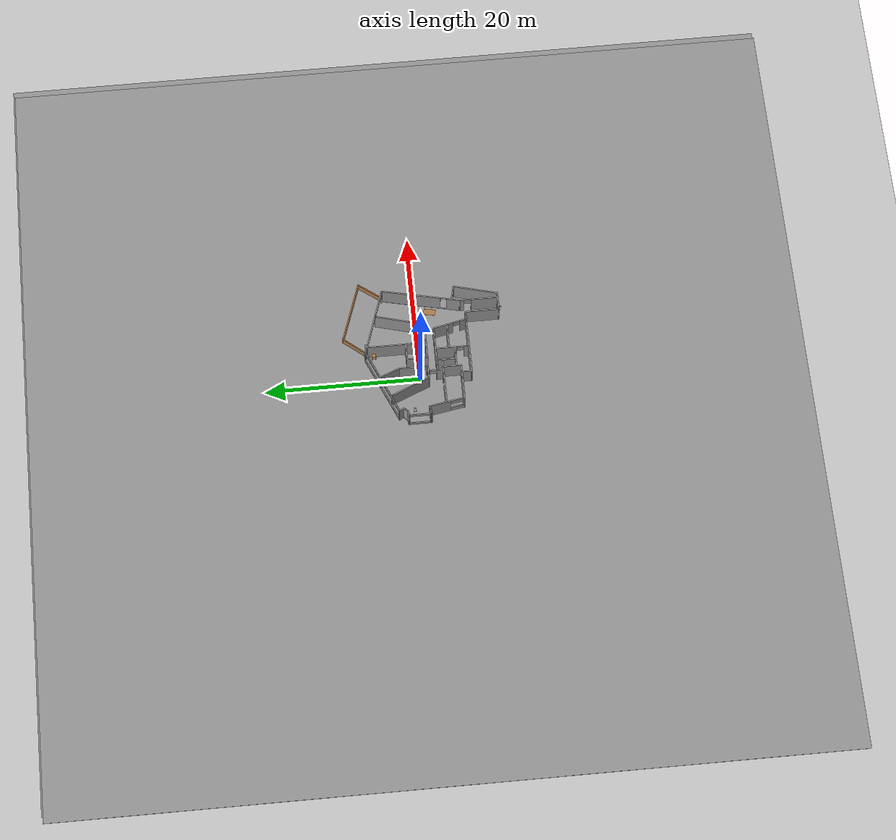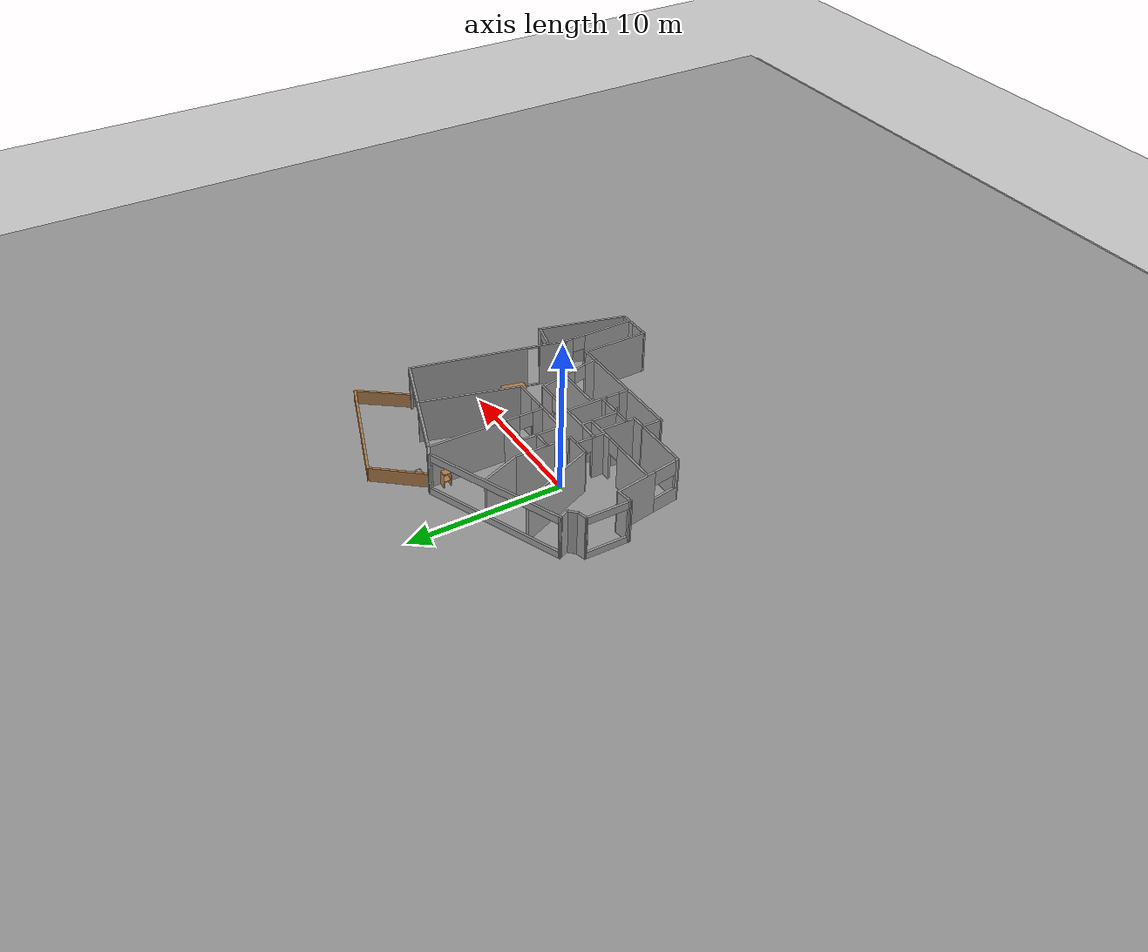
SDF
<sdf version="1.6">
 <world name="default">
  <plugin name="hello" filename="libhello.so"/>
  <light name="sun" type="directional">
   <pose>0 0 10 0 -0 0</pose>
   <diffuse>0.8 0.8 0.8 1</diffuse>
   <specular>0.2 0.2 0.2 1</specular>
   <attenuation>
    <range>1000</range>
    <constant>0.9</constant>
    <linear>0.01</linear>
    <quadratic>0.001</quadratic>
   </attenuation>
   <direction>-0.5 0.1 -0.9</direction>
  </light>
  <model name="ground_plane">
   <static>1</static>
   <link name="link">
    <collision name="collision">
     <geometry><plane><normal>0 0 1</normal><size>100 100</size></plane></geometry>
     <surface>
      <contact><collide_bitmask>65535</collide_bitmask></contact>
      <friction><ode><mu>100</mu><mu2>50</mu2></ode></friction>
     </surface>
    </collision>
    <visual name="visual">
     <cast_shadows>0</cast_shadows>
     <geometry><plane><normal>0 0 1</normal><size>100 100</size></plane></geometry>
     <material>
      <script><uri>file://media/materials/scripts/gazebo.material</uri><name>Gazebo/Grey</name></script>
     </material>
    </visual>
   </link>
  </model>
  <gravity>0 0 -9.8</gravity>
  <magnetic_field>6e-06 2.3e-05 -4.2e-05</magnetic_field>
  <atmosphere type="adiabatic"/>
  <physics name="default_physics" default="0" type="ode">
   <max_step_size>0.001</max_step_size>
   <real_time_factor>1</real_time_factor>
   <real_time_update_rate>1000</real_time_update_rate>
  </physics>
  <scene><ambient>0.4 0.4 0.4 1</ambient><background>0.7 0.7 0.7 1</background><shadows>1</shadows></scene>
  <spherical_coordinates>
   <surface_model>EARTH_WGS84</surface_model>
   <latitude_deg>0</latitude_deg>
   <longitude_deg>0</longitude_deg>
   <elevation>0</elevation>
   <heading_deg>0</heading_deg>
  </spherical_coordinates>
  <model name="FourWheel">
   <link name="link_0">
    <inertial>
     <mass>1</mass>
     <inertia>
      <ixx>0.166667</ixx>
      <ixy>0</ixy>
      <ixz>0</ixz>
      <iyy>0.166667</iyy>
      <iyz>0</iyz>
      <izz>0.166667</izz>
     </inertia>
    </inertial>
    <pose>0 -0 0.1 0 -0 0</pose>
    <visual name="visual">
     <geometry><box><size>0.6 0.3 0.1</size></box></geometry>
     <material>
      <lighting>1</lighting>
      <script><uri>file://media/materials/scripts/gazebo.material</uri><name>Gazebo/Grey</name></script>
      <shader type="pixel"><normal_map>__default__</normal_map></shader>
      <ambient>0.3 0.3 0.3 1</ambient>
      <diffuse>0.7 0.7 0.7 1</diffuse>
      <specular>0.01 0.01 0.01 1</specular>
      <emissive>0 0 0 1</emissive>
     </material>
    </visual>
    <collision name="collision">
     <geometry><box><size>0.6 0.3 0.1</size></box></geometry>
     <surface>
      <friction>
       <ode><mu>1</mu><mu2>1</mu2><fdir1>0 0 0</fdir1><slip1>0</slip1><slip2>0</slip2></ode>
       <torsional>
        <coefficient>1</coefficient>
        <patch_radius>0</patch_radius>
        <surface_radius>0</surface_radius>
        <use_patch_radius>1</use_patch_radius>
        <ode><slip>0</slip></ode>
       </torsional>
      </friction>
      <bounce><restitution_coefficient>0</restitution_coefficient><threshold>1e+06</threshold></bounce>
      <contact>
       <collide_without_contact>0</collide_without_contact>
       <collide_without_contact_bitmask>1</collide_without_contact_bitmask>
       <collide_bitmask>1</collide_bitmask>
       <ode>
        <soft_cfm>0</soft_cfm>
        <soft_erp>0.2</soft_erp>
        <kp>1e+13</kp>
        <kd>1</kd>
        <max_vel>0.01</max_vel>
        <min_depth>0</min_depth>
       </ode>
       <bullet>
        <split_impulse>1</split_impulse>
        <split_impulse_penetration_threshold>-0.01</split_impulse_penetration_threshold>
        <soft_cfm>0</soft_cfm>
        <soft_erp>0.2</soft_erp>
        <kp>1e+13</kp>
        <kd>1</kd>
       </bullet>
      </contact>
     </surface>
    </collision>
   </link>
   <link name="link_2">
    <inertial>
     <mass>1</mass>
     <inertia><ixx>0.145833</ixx><ixy>0</ixy><ixz>0</ixz><iyy>0.145833</iyy><iyz>0</iyz><izz>0.125</izz></inertia>
    </inertial>
    <pose>-0.2 -0.175013 0.1 1.5707 -0 0</pose>
    <visual name="visual">
     <geometry><cylinder><radius>0.1</radius><length>0.05</length></cylinder></geometry>
     <material>
      <lighting>1</lighting>
      <script><uri>file://media/materials/scripts/gazebo.material</uri><name>Gazebo/Grey</name></script>
      <shader type="pixel"><normal_map>__default__</normal_map></shader>
      <ambient>0.3 0.3 0.3 1</ambient>
      <diffuse>0.7 0.7 0.7 1</diffuse>
      <specular>0.01 0.01 0.01 1</specular>
      <emissive>0 0 0 1</emissive>
     </material>
    </visual>
    <collision name="collision">
     <geometry><cylinder><radius>0.1</radius><length>0.05</length></cylinder></geometry>
     <surface>
      <friction>
       <ode><mu>1</mu><mu2>1</mu2><fdir1>0 0 0</fdir1><slip1>0</slip1><slip2>0</slip2></ode>
       <torsional>
        <coefficient>1</coefficient>
        <patch_radius>0</patch_radius>
        <surface_radius>0</surface_radius>
        <use_patch_radius>1</use_patch_radius>
        <ode><slip>0</slip></ode>
       </torsional>
      </friction>
      <bounce><restitution_coefficient>0</restitution_coefficient><threshold>1e+06</threshold></bounce>
      <contact>
       <collide_without_contact>0</collide_without_contact>
       <collide_without_contact_bitmask>1</collide_without_contact_bitmask>
       <collide_bitmask>1</collide_bitmask>
       <ode>
        <soft_cfm>0</soft_cfm>
        <soft_erp>0.2</soft_erp>
        <kp>1e+13</kp>
        <kd>1</kd>
        <max_vel>0.01</max_vel>
        <min_depth>0</min_depth>
       </ode>
       <bullet>
        <split_impulse>1</split_impulse>
        <split_impulse_penetration_threshold>-0.01</split_impulse_penetration_threshold>
        <soft_cfm>0</soft_cfm>
        <soft_erp>0.2</soft_erp>
        <kp>1e+13</kp>
        <kd>1</kd>
       </bullet>
      </contact>
     </surface>
    </collision>
   </link>
   <link name="link_2_clone">
    <inertial>
     <mass>1</mass>
     <inertia><ixx>0.145833</ixx><ixy>0</ixy><ixz>0</ixz><iyy>0.145833</iyy><iyz>0</iyz><izz>0.125</izz></inertia>
    </inertial>
    <pose>0.2 -0.12499 0.1 1.5707 -0 0</pose>
    <visual name="visual">
     <geometry><cylinder><radius>0.1</radius><length>0.05</length></cylinder></geometry>
     <material>
      <lighting>1</lighting>
      <script><uri>file://media/materials/scripts/gazebo.material</uri><name>Gazebo/Grey</name></script>
      <shader type="pixel"><normal_map>__default__</normal_map></shader>
      <ambient>0.3 0.3 0.3 1</ambient>
      <diffuse>0.7 0.7 0.7 1</diffuse>
      <specular>0.01 0.01 0.01 1</specular>
      <emissive>0 0 0 1</emissive>
     </material>
    </visual>
    <collision name="collision">
     <geometry><cylinder><radius>0.1</radius><length>0.05</length></cylinder></geometry>
     <surface>
      <friction>
       <ode><mu>1</mu><mu2>1</mu2><fdir1>0 0 0</fdir1><slip1>0</slip1><slip2>0</slip2></ode>
       <torsional>
        <coefficient>1</coefficient>
        <patch_radius>0</patch_radius>
        <surface_radius>0</surface_radius>
        <use_patch_radius>1</use_patch_radius>
        <ode><slip>0</slip></ode>
       </torsional>
      </friction>
      <bounce><restitution_coefficient>0</restitution_coefficient><threshold>1e+06</threshold></bounce>
      <contact>
       <collide_without_contact>0</collide_without_contact>
       <collide_without_contact_bitmask>1</collide_without_contact_bitmask>
       <collide_bitmask>1</collide_bitmask>
       <ode>
        <soft_cfm>0</soft_cfm>
        <soft_erp>0.2</soft_erp>
        <kp>1e+13</kp>
        <kd>1</kd>
        <max_vel>0.01</max_vel>
        <min_depth>0</min_depth>
       </ode>
       <bullet>
        <split_impulse>1</split_impulse>
        <split_impulse_penetration_threshold>-0.01</split_impulse_penetration_threshold>
        <soft_cfm>0</soft_cfm>
        <soft_erp>0.2</soft_erp>
        <kp>1e+13</kp>
        <kd>1</kd>
       </bullet>
      </contact>
     </surface>
    </collision>
   </link>
   <link name="link_2_clone_0">
    <inertial>
     <mass>1</mass>
     <inertia><ixx>0.145833</ixx><ixy>0</ixy><ixz>0</ixz><iyy>0.145833</iyy><iyz>0</iyz><izz>0.125</izz></inertia>
    </inertial>
    <pose>0.2 0.12499 0.1 1.5707 -0 0</pose>
    <visual name="visual">
     <geometry><cylinder><radius>0.1</radius><length>0.05</length></cylinder></geometry>
     <material>
      <lighting>1</lighting>
      <script><uri>file://media/materials/scripts/gazebo.material</uri><name>Gazebo/Grey</name></script>
      <shader type="pixel"><normal_map>__default__</normal_map></shader>
      <ambient>0.3 0.3 0.3 1</ambient>
      <diffuse>0.7 0.7 0.7 1</diffuse>
      <specular>0.01 0.01 0.01 1</specular>
      <emissive>0 0 0 1</emissive>
     </material>
    </visual>
    <collision name="collision">
     <geometry><cylinder><radius>0.1</radius><length>0.05</length></cylinder></geometry>
     <surface>
      <friction>
       <ode><mu>1</mu><mu2>1</mu2><fdir1>0 0 0</fdir1><slip1>0</slip1><slip2>0</slip2></ode>
       <torsional>
        <coefficient>1</coefficient>
        <patch_radius>0</patch_radius>
        <surface_radius>0</surface_radius>
        <use_patch_radius>1</use_patch_radius>
        <ode><slip>0</slip></ode>
       </torsional>
      </friction>
      <bounce><restitution_coefficient>0</restitution_coefficient><threshold>1e+06</threshold></bounce>
      <contact>
       <collide_without_contact>0</collide_without_contact>
       <collide_without_contact_bitmask>1</collide_without_contact_bitmask>
       <collide_bitmask>1</collide_bitmask>
       <ode>
        <soft_cfm>0</soft_cfm>
        <soft_erp>0.2</soft_erp>
        <kp>1e+13</kp>
        <kd>1</kd>
        <max_vel>0.01</max_vel>
        <min_depth>0</min_depth>
       </ode>
       <bullet>
        <split_impulse>1</split_impulse>
        <split_impulse_penetration_threshold>-0.01</split_impulse_penetration_threshold>
        <soft_cfm>0</soft_cfm>
        <soft_erp>0.2</soft_erp>
        <kp>1e+13</kp>
        <kd>1</kd>
       </bullet>
      </contact>
     </surface>
    </collision>
   </link>
   <link name="link_2_clone_1">
    <inertial>
     <mass>1</mass>
     <inertia><ixx>0.145833</ixx><ixy>0</ixy><ixz>0</ixz><iyy>0.145833</iyy><iyz>0</iyz><izz>0.125</izz></inertia>
    </inertial>
    <pose>-0.2 0.12499 0.1 1.5707 -0 0</pose>
    <visual name="visual">
     <geometry><cylinder><radius>0.1</radius><length>0.05</length></cylinder></geometry>
     <material>
      <lighting>1</lighting>
      <script><uri>file://media/materials/scripts/gazebo.material</uri><name>Gazebo/Grey</name></script>
      <shader type="pixel"><normal_map>__default__</normal_map></shader>
      <ambient>0.3 0.3 0.3 1</ambient>
      <diffuse>0.7 0.7 0.7 1</diffuse>
      <specular>0.01 0.01 0.01 1</specular>
      <emissive>0 0 0 1</emissive>
     </material>
    </visual>
    <collision name="collision">
     <geometry><cylinder><radius>0.1</radius><length>0.05</length></cylinder></geometry>
     <surface>
      <friction>
       <ode><mu>1</mu><mu2>1</mu2><fdir1>0 0 0</fdir1><slip1>0</slip1><slip2>0</slip2></ode>
       <torsional>
        <coefficient>1</coefficient>
        <patch_radius>0</patch_radius>
        <surface_radius>0</surface_radius>
        <use_patch_radius>1</use_patch_radius>
        <ode><slip>0</slip></ode>
       </torsional>
      </friction>
      <bounce><restitution_coefficient>0</restitution_coefficient><threshold>1e+06</threshold></bounce>
      <contact>
       <collide_without_contact>0</collide_without_contact>
       <collide_without_contact_bitmask>1</collide_without_contact_bitmask>
       <collide_bitmask>1</collide_bitmask>
       <ode>
        <soft_cfm>0</soft_cfm>
        <soft_erp>0.2</soft_erp>
        <kp>1e+13</kp>
        <kd>1</kd>
        <max_vel>0.01</max_vel>
        <min_depth>0</min_depth>
       </ode>
       <bullet>
        <split_impulse>1</split_impulse>
        <split_impulse_penetration_threshold>-0.01</split_impulse_penetration_threshold>
        <soft_cfm>0</soft_cfm>
        <soft_erp>0.2</soft_erp>
        <kp>1e+13</kp>
        <kd>1</kd>
       </bullet>
      </contact>
     </surface>
    </collision>
   </link>
   <joint name="link_0_JOINT_2" type="revolute">
    <parent>link_0</parent>
    <child>link_2</child>
    <axis>
     <xyz>1 0 0</xyz>
     <use_parent_model_frame>0</use_parent_model_frame>
     <limit>
      <lower>-1.79769e+308</lower>
      <upper>1.79769e+308</upper>
      <effort>-1</effort>
      <velocity>-1</velocity>
     </limit>
     <dynamics>
      <spring_reference>0</spring_reference>
      <spring_stiffness>0</spring_stiffness>
      <damping>0</damping>
     </dynamics>
    </axis>
    <physics>
     <ode><limit><cfm>0</cfm><erp>0.2</erp></limit><suspension><cfm>0</cfm><erp>0.2</erp></suspension></ode>
    </physics>
   </joint>
   <joint name="link_0_JOINT_3" type="revolute">
    <parent>link_0</parent>
    <child>link_2_clone_0</child>
    <axis>
     <xyz>1 0 0</xyz>
     <use_parent_model_frame>0</use_parent_model_frame>
     <limit>
      <lower>-1.79769e+308</lower>
      <upper>1.79769e+308</upper>
      <effort>-1</effort>
      <velocity>-1</velocity>
     </limit>
     <dynamics>
      <spring_reference>0</spring_reference>
      <spring_stiffness>0</spring_stiffness>
      <damping>0</damping>
     </dynamics>
    </axis>
    <physics>
     <ode><limit><cfm>0</cfm><erp>0.2</erp></limit><suspension><cfm>0</cfm><erp>0.2</erp></suspension></ode>
    </physics>
   </joint>
   <joint name="link_0_JOINT_4" type="revolute">
    <parent>link_0</parent>
    <child>link_2_clone_1</child>
    <axis>
     <xyz>1 0 0</xyz>
     <use_parent_model_frame>0</use_parent_model_frame>
     <limit>
      <lower>-1.79769e+308</lower>
      <upper>1.79769e+308</upper>
      <effort>-1</effort>
      <velocity>-1</velocity>
     </limit>
     <dynamics>
      <spring_reference>0</spring_reference>
      <spring_stiffness>0</spring_stiffness>
      <damping>0</damping>
     </dynamics>
    </axis>
    <physics>
     <ode><limit><cfm>0</cfm><erp>0.2</erp></limit><suspension><cfm>0</cfm><erp>0.2</erp></suspension></ode>
    </physics>
   </joint>
   <joint name="link_0_JOINT_5" type="revolute">
    <parent>link_0</parent>
    <child>link_2_clone</child>
    <axis>
     <xyz>1 0 0</xyz>
     <use_parent_model_frame>0</use_parent_model_frame>
     <limit>
      <lower>-1.79769e+308</lower>
      <upper>1.79769e+308</upper>
      <effort>-1</effort>
      <velocity>-1</velocity>
     </limit>
     <dynamics>
      <spring_reference>0</spring_reference>
      <spring_stiffness>0</spring_stiffness>
      <damping>0</damping>
     </dynamics>
    </axis>
    <physics>
     <ode><limit><cfm>0</cfm><erp>0.2</erp></limit><suspension><cfm>0</cfm><erp>0.2</erp></suspension></ode>
    </physics>
   </joint>
   <static>0</static>
   <pose>-0.001537 -0.003627 -1e-06 5e-06 4e-06 -0.012993</pose>
  </model>
  <model name="Leedon">
   <pose>3.85043 -0.63069 0 0 -0 0</pose>
   <link name="Wall_0">
    <pose>-0.03016 3.43412 0 0 -0 -1.5708</pose>
    <visual name="Wall_0_Visual_0">
     <pose>-0.847654 0 1.5 0 -0 0</pose>
     <geometry><box><size>6.05469 0.15 3</size></box></geometry>
     <material>
      <script><uri>file://media/materials/scripts/gazebo.material</uri><name>Gazebo/Grey</name></script>
      <ambient>1 1 1 1</ambient>
     </material>
     <meta><layer>0</layer></meta>
    </visual>
    <collision name="Wall_0_Collision_0">
     <geometry><box><size>6.05469 0.15 3</size></box></geometry>
     <pose>-0.847654 0 1.5 0 -0 0</pose>
    </collision>
    <visual name="Wall_0_Visual_1">
     <pose>3.47735 0 1.5 0 -0 0</pose>
     <geometry><box><size>0.795308 0.15 3</size></box></geometry>
     <material>
      <script><uri>file://media/materials/scripts/gazebo.material</uri><name>Gazebo/Grey</name></script>
      <ambient>1 1 1 1</ambient>
     </material>
     <meta><layer>0</layer></meta>
    </visual>
    <collision name="Wall_0_Collision_1">
     <geometry><box><size>0.795308 0.15 3</size></box></geometry>
     <pose>3.47735 0 1.5 0 -0 0</pose>
    </collision>
    <visual name="Wall_0_Visual_2">
     <pose>2.62969 0 2.5 0 -0 0</pose>
     <geometry><box><size>0.9 0.15 1</size></box></geometry>
     <material>
      <script><uri>file://media/materials/scripts/gazebo.material</uri><name>Gazebo/Grey</name></script>
      <ambient>1 1 1 1</ambient>
     </material>
     <meta><layer>0</layer></meta>
    </visual>
    <collision name="Wall_0_Collision_2">
     <geometry><box><size>0.9 0.15 1</size></box></geometry>
     <pose>2.62969 0 2.5 0 -0 0</pose>
    </collision>
   </link>
   <link name="Wall_1">
    <collision name="Wall_1_Collision">
     <geometry><box><size>2.24982 0.15 3</size></box></geometry>
     <pose>0 0 1.5 0 -0 0</pose>
    </collision>
    <visual name="Wall_1_Visual">
     <pose>0 0 1.5 0 -0 0</pose>
     <geometry><box><size>2.24982 0.15 3</size></box></geometry>
     <material>
      <script><uri>file://media/materials/scripts/gazebo.material</uri><name>Gazebo/Grey</name></script>
      <ambient>1 1 1 1</ambient>
     </material>
     <meta><layer>0</layer></meta>
    </visual>
    <pose>-1.08016 -0.365879 0 0 -0 3.14159</pose>
   </link>
   <link name="Wall_12">
    <collision name="Wall_12_Collision">
     <geometry><box><size>1.75 0.15 3</size></box></geometry>
     <pose>0 0 1.5 0 -0 0</pose>
    </collision>
    <visual name="Wall_12_Visual">
     <pose>0 0 1.5 0 -0 0</pose>
     <geometry><box><size>1.75 0.15 3</size></box></geometry>
     <material>
      <script><uri>file://media/materials/scripts/gazebo.material</uri><name>Gazebo/Grey</name></script>
      <ambient>1 1 1 1</ambient>
     </material>
     <meta><layer>0</layer></meta>
    </visual>
    <pose>-4.10616 -0.297879 0 0 -0 0</pose>
   </link>
   <link name="Wall_13">
    <pose>-3.31066 1.52712 0 0 -0 1.57326</pose>
    <visual name="Wall_13_Visual_0">
     <pose>-1.77975 0 1.5 0 -0 0</pose>
     <geometry><box><size>0.240493 0.15 3</size></box></geometry>
     <material>
      <script><uri>file://media/materials/scripts/gazebo.material</uri><name>Gazebo/Grey</name></script>
      <ambient>1 1 1 1</ambient>
     </material>
     <meta><layer>0</layer></meta>
    </visual>
    <collision name="Wall_13_Collision_0">
     <geometry><box><size>0.240493 0.15 3</size></box></geometry>
     <pose>-1.77975 0 1.5 0 -0 0</pose>
    </collision>
    <visual name="Wall_13_Visual_1">
     <pose>0.570247 0 1.5 0 -0 0</pose>
     <geometry><box><size>2.65951 0.15 3</size></box></geometry>
     <material>
      <script><uri>file://media/materials/scripts/gazebo.material</uri><name>Gazebo/Grey</name></script>
      <ambient>1 1 1 1</ambient>
     </material>
     <meta><layer>0</layer></meta>
    </visual>
    <collision name="Wall_13_Collision_1">
     <geometry><box><size>2.65951 0.15 3</size></box></geometry>
     <pose>0.570247 0 1.5 0 -0 0</pose>
    </collision>
    <visual name="Wall_13_Visual_2">
     <pose>-1.20951 0 2.5 0 -0 0</pose>
     <geometry><box><size>0.9 0.15 1</size></box></geometry>
     <material>
      <script><uri>file://media/materials/scripts/gazebo.material</uri><name>Gazebo/Grey</name></script>
      <ambient>1 1 1 1</ambient>
     </material>
     <meta><layer>0</layer></meta>
    </visual>
    <collision name="Wall_13_Collision_2">
     <geometry><box><size>0.9 0.15 1</size></box></geometry>
     <pose>-1.20951 0 2.5 0 -0 0</pose>
    </collision>
   </link>
   <link name="Wall_14">
    <collision name="Wall_14_Collision">
     <geometry><box><size>2.76478 0.15 3</size></box></geometry>
     <pose>0 0 1.5 0 -0 0</pose>
    </collision>
    <visual name="Wall_14_Visual">
     <pose>0 0 1.5 0 -0 0</pose>
     <geometry><box><size>2.76478 0.15 3</size></box></geometry>
     <material>
      <script><uri>file://media/materials/scripts/gazebo.material</uri><name>Gazebo/Grey</name></script>
      <ambient>1 1 1 1</ambient>
     </material>
     <meta><layer>0</layer></meta>
    </visual>
    <pose>-3.80166 4.56562 0 0 -0 1.95208</pose>
   </link>
   <link name="Wall_16">
    <collision name="Wall_16_Collision">
     <geometry><box><size>5.5 0.15 3</size></box></geometry>
     <pose>0 0 1.5 0 -0 0</pose>
    </collision>
    <visual name="Wall_16_Visual">
     <pose>0 0 1.5 0 -0 0</pose>
     <geometry><box><size>5.5 0.15 3</size></box></geometry>
     <material>
      <script><uri>file://media/materials/scripts/gazebo.material</uri><name>Gazebo/Grey</name></script>
      <ambient>1 1 1 1</ambient>
     </material>
     <meta><layer>0</layer></meta>
    </visual>
    <pose>-5.94416 2.16762 0 0 -0 1.96928</pose>
   </link>
   <link name="Wall_18">
    <collision name="Wall_18_Collision">
     <geometry><box><size>4.5 0.15 3</size></box></geometry>
     <pose>0 0 1.5 0 -0 0</pose>
    </collision>
    <visual name="Wall_18_Visual">
     <pose>0 0 1.5 0 -0 0</pose>
     <geometry><box><size>4.5 0.15 3</size></box></geometry>
     <material>
      <script><uri>file://media/materials/scripts/gazebo.material</uri><name>Gazebo/Grey</name></script>
      <ambient>1 1 1 1</ambient>
     </material>
     <meta><layer>0</layer></meta>
    </visual>
    <pose>3.83384 -7.96688 0 0 -0 1.5708</pose>
   </link>
   <link name="Wall_19">
    <collision name="Wall_19_Collision">
     <geometry><box><size>8.5 0.15 3</size></box></geometry>
     <pose>0 0 1.5 0 -0 0</pose>
    </collision>
    <visual name="Wall_19_Visual">
     <pose>0 0 1.5 0 -0 0</pose>
     <geometry><box><size>8.5 0.15 3</size></box></geometry>
     <material>
      <script><uri>file://media/materials/scripts/gazebo.material</uri><name>Gazebo/Grey</name></script>
      <ambient>1 1 1 1</ambient>
     </material>
     <meta><layer>0</layer></meta>
    </visual>
    <pose>-0.34116 -5.79188 0 0 -0 3.14159</pose>
   </link>
   <link name="Wall_2">
    <collision name="Wall_2_Collision">
     <geometry><box><size>2.75 0.15 3</size></box></geometry>
     <pose>0 0 1.5 0 -0 0</pose>
    </collision>
    <visual name="Wall_2_Visual">
     <pose>0 0 1.5 0 -0 0</pose>
     <geometry><box><size>2.75 0.15 3</size></box></geometry>
     <material>
      <script><uri>file://media/materials/scripts/gazebo.material</uri><name>Gazebo/Grey</name></script>
      <ambient>1 1 1 1</ambient>
     </material>
     <meta><layer>0</layer></meta>
    </visual>
    <pose>-2.13016 0.934121 0 0 -0 1.5708</pose>
   </link>
   <link name="Wall_20">
    <collision name="Wall_20_Collision">
     <geometry><box><size>1.4062 0.15 3</size></box></geometry>
     <pose>0 0 1.5 0 -0 0</pose>
    </collision>
    <visual name="Wall_20_Visual">
     <pose>0 0 1.5 0 -0 0</pose>
     <geometry><box><size>1.4062 0.15 3</size></box></geometry>
     <material>
      <script><uri>file://media/materials/scripts/gazebo.material</uri><name>Gazebo/Grey</name></script>
      <ambient>1 1 1 1</ambient>
     </material>
     <meta><layer>0</layer></meta>
    </visual>
    <pose>-4.51366 -5.16388 0 0 -0 1.56682</pose>
   </link>
   <link name="Wall_23">
    <pose>5.52684 -7.69588 0 0 -0 1.5708</pose>
    <visual name="Wall_23_Visual_0">
     <pose>-0.760615 0 1.5 0 -0 0</pose>
     <geometry><box><size>3.51267 0.15 3</size></box></geometry>
     <material>
      <script><uri>file://media/materials/scripts/gazebo.material</uri><name>Gazebo/Grey</name></script>
      <ambient>1 1 1 1</ambient>
     </material>
     <meta><layer>0</layer></meta>
    </visual>
    <collision name="Wall_23_Collision_0">
     <geometry><box><size>3.51267 0.15 3</size></box></geometry>
     <pose>-0.760615 0 1.5 0 -0 0</pose>
    </collision>
    <visual name="Wall_23_Visual_1">
     <pose>2.20634 0 1.5 0 -0 0</pose>
     <geometry><box><size>0.621229 0.15 3</size></box></geometry>
     <material>
      <script><uri>file://media/materials/scripts/gazebo.material</uri><name>Gazebo/Grey</name></script>
      <ambient>1 1 1 1</ambient>
     </material>
     <meta><layer>0</layer></meta>
    </visual>
    <collision name="Wall_23_Collision_1">
     <geometry><box><size>0.621229 0.15 3</size></box></geometry>
     <pose>2.20634 0 1.5 0 -0 0</pose>
    </collision>
    <visual name="Wall_23_Visual_2">
     <pose>1.44572 0 2.5 0 -0 0</pose>
     <geometry><box><size>0.9 0.15 1</size></box></geometry>
     <material>
      <script><uri>file://media/materials/scripts/gazebo.material</uri><name>Gazebo/Grey</name></script>
      <ambient>1 1 1 1</ambient>
     </material>
     <meta><layer>0</layer></meta>
    </visual>
    <collision name="Wall_23_Collision_2">
     <geometry><box><size>0.9 0.15 1</size></box></geometry>
     <pose>1.44572 0 2.5 0 -0 0</pose>
    </collision>
   </link>
   <link name="Wall_28">
    <pose>-1.04316 -1.51288 0 0 -0 3.14159</pose>
    <visual name="Wall_28_Visual_0">
     <pose>-2.3836 0 1.5 0 -0 0</pose>
     <geometry><box><size>1.23281 0.15 3</size></box></geometry>
     <material>
      <script><uri>file://media/materials/scripts/gazebo.material</uri><name>Gazebo/Grey</name></script>
      <ambient>1 1 1 1</ambient>
     </material>
     <meta><layer>0</layer></meta>
    </visual>
    <collision name="Wall_28_Collision_0">
     <geometry><box><size>1.23281 0.15 3</size></box></geometry>
     <pose>-2.3836 0 1.5 0 -0 0</pose>
    </collision>
    <visual name="Wall_28_Visual_1">
     <pose>0.449055 0 1.5 0 -0 0</pose>
     <geometry><box><size>2.6325 0.15 3</size></box></geometry>
     <material>
      <script><uri>file://media/materials/scripts/gazebo.material</uri><name>Gazebo/Grey</name></script>
      <ambient>1 1 1 1</ambient>
     </material>
     <meta><layer>0</layer></meta>
    </visual>
    <collision name="Wall_28_Collision_1">
     <geometry><box><size>2.6325 0.15 3</size></box></geometry>
     <pose>0.449055 0 1.5 0 -0 0</pose>
    </collision>
    <visual name="Wall_28_Visual_2">
     <pose>2.83265 0 1.5 0 -0 0</pose>
     <geometry><box><size>0.334695 0.15 3</size></box></geometry>
     <material>
      <script><uri>file://media/materials/scripts/gazebo.material</uri><name>Gazebo/Grey</name></script>
      <ambient>1 1 1 1</ambient>
     </material>
     <meta><layer>0</layer></meta>
    </visual>
    <collision name="Wall_28_Collision_2">
     <geometry><box><size>0.334695 0.15 3</size></box></geometry>
     <pose>2.83265 0 1.5 0 -0 0</pose>
    </collision>
    <visual name="Wall_28_Visual_3">
     <pose>-1.31719 0 2.5 0 -0 0</pose>
     <geometry><box><size>0.9 0.15 1</size></box></geometry>
     <material>
      <script><uri>file://media/materials/scripts/gazebo.material</uri><name>Gazebo/Grey</name></script>
      <ambient>1 1 1 1</ambient>
     </material>
     <meta><layer>0</layer></meta>
    </visual>
    <collision name="Wall_28_Collision_3">
     <geometry><box><size>0.9 0.15 1</size></box></geometry>
     <pose>-1.31719 0 2.5 0 -0 0</pose>
    </collision>
    <visual name="Wall_28_Visual_4">
     <pose>2.2153 0 2.5 0 -0 0</pose>
     <geometry><box><size>0.9 0.15 1</size></box></geometry>
     <material>
      <script><uri>file://media/materials/scripts/gazebo.material</uri><name>Gazebo/Grey</name></script>
      <ambient>1 1 1 1</ambient>
     </material>
     <meta><layer>0</layer></meta>
    </visual>
    <collision name="Wall_28_Collision_4">
     <geometry><box><size>0.9 0.15 1</size></box></geometry>
     <pose>2.2153 0 2.5 0 -0 0</pose>
    </collision>
   </link>
   <link name="Wall_3">
    <collision name="Wall_3_Collision">
     <geometry><box><size>2.24982 0.15 3</size></box></geometry>
     <pose>0 0 1.5 0 -0 0</pose>
    </collision>
    <visual name="Wall_3_Visual">
     <pose>0 0 1.5 0 -0 0</pose>
     <geometry><box><size>2.24982 0.15 3</size></box></geometry>
     <material>
      <script><uri>file://media/materials/scripts/gazebo.material</uri><name>Gazebo/Grey</name></script>
      <ambient>1 1 1 1</ambient>
     </material>
     <meta><layer>0</layer></meta>
    </visual>
    <pose>-1.08016 2.23412 0 0 -0 0</pose>
   </link>
   <link name="Wall_30">
    <pose>-3.96916 -1.28188 0 0 -0 1.5708</pose>
    <visual name="Wall_30_Visual_0">
     <pose>-0.540622 0 1.5 0 -0 0</pose>
     <geometry><box><size>0.918757 0.15 3</size></box></geometry>
     <material>
      <script><uri>file://media/materials/scripts/gazebo.material</uri><name>Gazebo/Grey</name></script>
      <ambient>1 1 1 1</ambient>
     </material>
     <meta><layer>0</layer></meta>
    </visual>
    <collision name="Wall_30_Collision_0">
     <geometry><box><size>0.918757 0.15 3</size></box></geometry>
     <pose>-0.540622 0 1.5 0 -0 0</pose>
    </collision>
    <visual name="Wall_30_Visual_1">
     <pose>0.909378 0 1.5 0 -0 0</pose>
     <geometry><box><size>0.181243 0.15 3</size></box></geometry>
     <material>
      <script><uri>file://media/materials/scripts/gazebo.material</uri><name>Gazebo/Grey</name></script>
      <ambient>1 1 1 1</ambient>
     </material>
     <meta><layer>0</layer></meta>
    </visual>
    <collision name="Wall_30_Collision_1">
     <geometry><box><size>0.181243 0.15 3</size></box></geometry>
     <pose>0.909378 0 1.5 0 -0 0</pose>
    </collision>
    <visual name="Wall_30_Visual_2">
     <pose>0.368757 0 2.5 0 -0 0</pose>
     <geometry><box><size>0.9 0.15 1</size></box></geometry>
     <material>
      <script><uri>file://media/materials/scripts/gazebo.material</uri><name>Gazebo/Grey</name></script>
      <ambient>1 1 1 1</ambient>
     </material>
     <meta><layer>0</layer></meta>
    </visual>
    <collision name="Wall_30_Collision_2">
     <geometry><box><size>0.9 0.15 1</size></box></geometry>
     <pose>0.368757 0 2.5 0 -0 0</pose>
    </collision>
   </link>
   <link name="Wall_32">
    <collision name="Wall_32_Collision">
     <geometry><box><size>2.5 0.15 3</size></box></geometry>
     <pose>0 0 1.5 0 -0 0</pose>
    </collision>
    <visual name="Wall_32_Visual">
     <pose>0 0 1.5 0 -0 0</pose>
     <geometry><box><size>2.5 0.15 3</size></box></geometry>
     <material>
      <script><uri>file://media/materials/scripts/gazebo.material</uri><name>Gazebo/Grey</name></script>
      <ambient>1 1 1 1</ambient>
     </material>
     <meta><layer>0</layer></meta>
    </visual>
    <pose>-2.58216 -2.72788 0 0 -0 -1.5708</pose>
   </link>
   <link name="Wall_35">
    <pose>-5.55416 -2.21488 0 0 -0 3.14159</pose>
    <visual name="Wall_35_Visual_0">
     <pose>-1.98221 0 1.5 0 -0 0</pose>
     <geometry><box><size>2.03558 0.15 3</size></box></geometry>
     <material>
      <script><uri>file://media/materials/scripts/gazebo.material</uri><name>Gazebo/Grey</name></script>
      <ambient>1 1 1 1</ambient>
     </material>
     <meta><layer>0</layer></meta>
    </visual>
    <collision name="Wall_35_Collision_0">
     <geometry><box><size>2.03558 0.15 3</size></box></geometry>
     <pose>-1.98221 0 1.5 0 -0 0</pose>
    </collision>
    <visual name="Wall_35_Visual_1">
     <pose>1.46779 0 1.5 0 -0 0</pose>
     <geometry><box><size>3.06442 0.15 3</size></box></geometry>
     <material>
      <script><uri>file://media/materials/scripts/gazebo.material</uri><name>Gazebo/Grey</name></script>
      <ambient>1 1 1 1</ambient>
     </material>
     <meta><layer>0</layer></meta>
    </visual>
    <collision name="Wall_35_Collision_1">
     <geometry><box><size>3.06442 0.15 3</size></box></geometry>
     <pose>1.46779 0 1.5 0 -0 0</pose>
    </collision>
    <visual name="Wall_35_Visual_2">
     <pose>-0.514423 0 2.5 0 -0 0</pose>
     <geometry><box><size>0.9 0.15 1</size></box></geometry>
     <material>
      <script><uri>file://media/materials/scripts/gazebo.material</uri><name>Gazebo/Grey</name></script>
      <ambient>1 1 1 1</ambient>
     </material>
     <meta><layer>0</layer></meta>
    </visual>
    <collision name="Wall_35_Collision_2">
     <geometry><box><size>0.9 0.15 1</size></box></geometry>
     <pose>-0.514423 0 2.5 0 -0 0</pose>
    </collision>
   </link>
   <link name="Wall_37">
    <pose>-0.98716 -3.68688 0 0 -0 -1.5708</pose>
    <visual name="Wall_37_Visual_0">
     <pose>-0.78688 0 1.5 0 -0 0</pose>
     <geometry><box><size>2.67624 0.15 3</size></box></geometry>
     <material>
      <script><uri>file://media/materials/scripts/gazebo.material</uri><name>Gazebo/Grey</name></script>
      <ambient>1 1 1 1</ambient>
     </material>
     <meta><layer>0</layer></meta>
    </visual>
    <collision name="Wall_37_Collision_0">
     <geometry><box><size>2.67624 0.15 3</size></box></geometry>
     <pose>-0.78688 0 1.5 0 -0 0</pose>
    </collision>
    <visual name="Wall_37_Visual_1">
     <pose>1.78812 0 1.5 0 -0 0</pose>
     <geometry><box><size>0.67376 0.15 3</size></box></geometry>
     <material>
      <script><uri>file://media/materials/scripts/gazebo.material</uri><name>Gazebo/Grey</name></script>
      <ambient>1 1 1 1</ambient>
     </material>
     <meta><layer>0</layer></meta>
    </visual>
    <collision name="Wall_37_Collision_1">
     <geometry><box><size>0.67376 0.15 3</size></box></geometry>
     <pose>1.78812 0 1.5 0 -0 0</pose>
    </collision>
    <visual name="Wall_37_Visual_2">
     <pose>1.00124 0 2.5 0 -0 0</pose>
     <geometry><box><size>0.9 0.15 1</size></box></geometry>
     <material>
      <script><uri>file://media/materials/scripts/gazebo.material</uri><name>Gazebo/Grey</name></script>
      <ambient>1 1 1 1</ambient>
     </material>
     <meta><layer>0</layer></meta>
    </visual>
    <collision name="Wall_37_Collision_2">
     <geometry><box><size>0.9 0.15 1</size></box></geometry>
     <pose>1.00124 0 2.5 0 -0 0</pose>
    </collision>
   </link>
   <link name="Wall_39">
    <collision name="Wall_39_Collision">
     <geometry><box><size>3.25 0.15 3</size></box></geometry>
     <pose>0 0 1.5 0 -0 0</pose>
    </collision>
    <visual name="Wall_39_Visual">
     <pose>0 0 1.5 0 -0 0</pose>
     <geometry><box><size>3.25 0.15 3</size></box></geometry>
     <material>
      <script><uri>file://media/materials/scripts/gazebo.material</uri><name>Gazebo/Grey</name></script>
      <ambient>1 1 1 1</ambient>
     </material>
     <meta><layer>0</layer></meta>
    </visual>
    <pose>0.56784 -3.26388 0 0 -0 0</pose>
   </link>
   <link name="Wall_41">
    <pose>2.35484 -3.66438 0 0 -0 1.7872</pose>
    <visual name="Wall_41_Visual_0">
     <pose>-1.79216 0 1.5 0 -0 0</pose>
     <geometry><box><size>0.971024 0.15 3</size></box></geometry>
     <material>
      <script><uri>file://media/materials/scripts/gazebo.material</uri><name>Gazebo/Grey</name></script>
      <ambient>1 1 1 1</ambient>
     </material>
     <meta><layer>0</layer></meta>
    </visual>
    <collision name="Wall_41_Collision_0">
     <geometry><box><size>0.971024 0.15 3</size></box></geometry>
     <pose>-1.79216 0 1.5 0 -0 0</pose>
    </collision>
    <visual name="Wall_41_Visual_1">
     <pose>0.935512 0 1.5 0 -0 0</pose>
     <geometry><box><size>2.68432 0.15 3</size></box></geometry>
     <material>
      <script><uri>file://media/materials/scripts/gazebo.material</uri><name>Gazebo/Grey</name></script>
      <ambient>1 1 1 1</ambient>
     </material>
     <meta><layer>0</layer></meta>
    </visual>
    <collision name="Wall_41_Collision_1">
     <geometry><box><size>2.68432 0.15 3</size></box></geometry>
     <pose>0.935512 0 1.5 0 -0 0</pose>
    </collision>
    <visual name="Wall_41_Visual_2">
     <pose>-0.856649 0 2.5 0 -0 0</pose>
     <geometry><box><size>0.9 0.15 1</size></box></geometry>
     <material>
      <script><uri>file://media/materials/scripts/gazebo.material</uri><name>Gazebo/Grey</name></script>
      <ambient>1 1 1 1</ambient>
     </material>
     <meta><layer>0</layer></meta>
    </visual>
    <collision name="Wall_41_Collision_2">
     <geometry><box><size>0.9 0.15 1</size></box></geometry>
     <pose>-0.856649 0 2.5 0 -0 0</pose>
    </collision>
   </link>
   <link name="Wall_45">
    <collision name="Wall_45_Collision">
     <geometry><box><size>0.75 0.15 3</size></box></geometry>
     <pose>0 0 1.5 0 -0 0</pose>
    </collision>
    <visual name="Wall_45_Visual">
     <pose>0 0 1.5 0 -0 0</pose>
     <geometry><box><size>0.75 0.15 3</size></box></geometry>
     <material>
      <script><uri>file://media/materials/scripts/gazebo.material</uri><name>Gazebo/Grey</name></script>
      <ambient>1 1 1 1</ambient>
     </material>
     <meta><layer>0</layer></meta>
    </visual>
    <pose>5.82684 -10.1379 0 0 -0 0</pose>
   </link>
   <link name="Wall_47">
    <collision name="Wall_47_Collision">
     <geometry><box><size>5.87389 0.15 3</size></box></geometry>
     <pose>0 0 1.5 0 -0 0</pose>
    </collision>
    <visual name="Wall_47_Visual">
     <pose>0 0 1.5 0 -0 0</pose>
     <geometry><box><size>5.87389 0.15 3</size></box></geometry>
     <material>
      <script><uri>file://media/materials/scripts/gazebo.material</uri><name>Gazebo/Grey</name></script>
      <ambient>1 1 1 1</ambient>
     </material>
     <meta><layer>0</layer></meta>
    </visual>
    <pose>6.85334 -7.36988 0 0 -0 -1.82747</pose>
   </link>
   <link name="Wall_49">
    <pose>6.68284 -4.39388 0 0 -0 -0.227857</pose>
    <visual name="Wall_49_Visual_0">
     <pose>-0.848793 0 1.5 0 -0 0</pose>
     <geometry><box><size>0.294331 0.15 3</size></box></geometry>
     <material>
      <script><uri>file://media/materials/scripts/gazebo.material</uri><name>Gazebo/Grey</name></script>
      <ambient>1 1 1 1</ambient>
     </material>
     <meta><layer>0</layer></meta>
    </visual>
    <collision name="Wall_49_Collision_0">
     <geometry><box><size>0.294331 0.15 3</size></box></geometry>
     <pose>-0.848793 0 1.5 0 -0 0</pose>
    </collision>
    <visual name="Wall_49_Visual_1">
     <pose>0.147165 0 0.5 0 -0 0</pose>
     <geometry><box><size>1.69759 0.15 1</size></box></geometry>
     <material>
      <script><uri>file://media/materials/scripts/gazebo.material</uri><name>Gazebo/Grey</name></script>
      <ambient>1 1 1 1</ambient>
     </material>
     <meta><layer>0</layer></meta>
    </visual>
    <collision name="Wall_49_Collision_1">
     <geometry><box><size>1.69759 0.15 1</size></box></geometry>
     <pose>0.147165 0 0.5 0 -0 0</pose>
    </collision>
    <visual name="Wall_49_Visual_2">
     <pose>0.785665 0 2 0 -0 0</pose>
     <geometry><box><size>0.420587 0.15 2</size></box></geometry>
     <material>
      <script><uri>file://media/materials/scripts/gazebo.material</uri><name>Gazebo/Grey</name></script>
      <ambient>1 1 1 1</ambient>
     </material>
     <meta><layer>0</layer></meta>
    </visual>
    <collision name="Wall_49_Collision_2">
     <geometry><box><size>0.420587 0.15 2</size></box></geometry>
     <pose>0.785665 0 2 0 -0 0</pose>
    </collision>
    <visual name="Wall_49_Visual_3">
     <pose>-0.063128 0 2.75 0 -0 0</pose>
     <geometry><box><size>1.277 0.15 0.5</size></box></geometry>
     <material>
      <script><uri>file://media/materials/scripts/gazebo.material</uri><name>Gazebo/Grey</name></script>
      <ambient>1 1 1 1</ambient>
     </material>
     <meta><layer>0</layer></meta>
    </visual>
    <collision name="Wall_49_Collision_3">
     <geometry><box><size>1.277 0.15 0.5</size></box></geometry>
     <pose>-0.063128 0 2.75 0 -0 0</pose>
    </collision>
   </link>
   <link name="Wall_5">
    <pose>1.26984 -0.365879 0 0 -0 0</pose>
    <visual name="Wall_5_Visual_0">
     <pose>-1.17066 0 1.5 0 -0 0</pose>
     <geometry><box><size>0.408674 0.15 3</size></box></geometry>
     <material>
      <script><uri>file://media/materials/scripts/gazebo.material</uri><name>Gazebo/Grey</name></script>
      <ambient>1 1 1 1</ambient>
     </material>
     <meta><layer>0</layer></meta>
    </visual>
    <collision name="Wall_5_Collision_0">
     <geometry><box><size>0.408674 0.15 3</size></box></geometry>
     <pose>-1.17066 0 1.5 0 -0 0</pose>
    </collision>
    <visual name="Wall_5_Visual_1">
     <pose>0.654337 0 1.5 0 -0 0</pose>
     <geometry><box><size>1.44133 0.15 3</size></box></geometry>
     <material>
      <script><uri>file://media/materials/scripts/gazebo.material</uri><name>Gazebo/Grey</name></script>
      <ambient>1 1 1 1</ambient>
     </material>
     <meta><layer>0</layer></meta>
    </visual>
    <collision name="Wall_5_Collision_1">
     <geometry><box><size>1.44133 0.15 3</size></box></geometry>
     <pose>0.654337 0 1.5 0 -0 0</pose>
    </collision>
    <visual name="Wall_5_Visual_2">
     <pose>-0.516326 0 2.5 0 -0 0</pose>
     <geometry><box><size>0.9 0.15 1</size></box></geometry>
     <material>
      <script><uri>file://media/materials/scripts/gazebo.material</uri><name>Gazebo/Grey</name></script>
      <ambient>1 1 1 1</ambient>
     </material>
     <meta><layer>0</layer></meta>
    </visual>
    <collision name="Wall_5_Collision_2">
     <geometry><box><size>0.9 0.15 1</size></box></geometry>
     <pose>-0.516326 0 2.5 0 -0 0</pose>
    </collision>
   </link>
   <link name="Wall_52">
    <collision name="Wall_52_Collision">
     <geometry><box><size>3.76077 0.15 3</size></box></geometry>
     <pose>0 0 1.5 0 -0 0</pose>
    </collision>
    <visual name="Wall_52_Visual">
     <pose>0 0 1.5 0 -0 0</pose>
     <geometry><box><size>3.76077 0.15 3</size></box></geometry>
     <material>
      <script><uri>file://media/materials/scripts/gazebo.material</uri><name>Gazebo/Grey</name></script>
      <ambient>1 1 1 1</ambient>
     </material>
     <meta><layer>0</layer></meta>
    </visual>
    <pose>-6.31666 -4.52888 0 0 -0 3.13772</pose>
   </link>
   <link name="Wall_54">
    <pose>-8.50166 -2.27988 0 0 -0 -1.40312</pose>
    <visual name="Wall_54_Visual_0">
     <pose>-0.939722 0 1.5 0 -0 0</pose>
     <geometry><box><size>2.81807 0.15 3</size></box></geometry>
     <material>
      <script><uri>file://media/materials/scripts/gazebo.material</uri><name>Gazebo/Grey</name></script>
      <ambient>1 1 1 1</ambient>
     </material>
     <meta><layer>0</layer></meta>
    </visual>
    <collision name="Wall_54_Collision_0">
     <geometry><box><size>2.81807 0.15 3</size></box></geometry>
     <pose>-0.939722 0 1.5 0 -0 0</pose>
    </collision>
    <visual name="Wall_54_Visual_1">
     <pose>1.40904 0 0.5 0 -0 0</pose>
     <geometry><box><size>1.87944 0.15 1</size></box></geometry>
     <material>
      <script><uri>file://media/materials/scripts/gazebo.material</uri><name>Gazebo/Grey</name></script>
      <ambient>1 1 1 1</ambient>
     </material>
     <meta><layer>0</layer></meta>
    </visual>
    <collision name="Wall_54_Collision_1">
     <geometry><box><size>1.87944 0.15 1</size></box></geometry>
     <pose>1.40904 0 0.5 0 -0 0</pose>
    </collision>
    <visual name="Wall_54_Visual_2">
     <pose>2.21054 0 2 0 -0 0</pose>
     <geometry><box><size>0.276444 0.15 2</size></box></geometry>
     <material>
      <script><uri>file://media/materials/scripts/gazebo.material</uri><name>Gazebo/Grey</name></script>
      <ambient>1 1 1 1</ambient>
     </material>
     <meta><layer>0</layer></meta>
    </visual>
    <collision name="Wall_54_Collision_2">
     <geometry><box><size>0.276444 0.15 2</size></box></geometry>
     <pose>2.21054 0 2 0 -0 0</pose>
    </collision>
    <visual name="Wall_54_Visual_3">
     <pose>1.27082 0 2.5 0 -0 0</pose>
     <geometry><box><size>1.603 0.15 1</size></box></geometry>
     <material>
      <script><uri>file://media/materials/scripts/gazebo.material</uri><name>Gazebo/Grey</name></script>
      <ambient>1 1 1 1</ambient>
     </material>
     <meta><layer>0</layer></meta>
    </visual>
    <collision name="Wall_54_Collision_3">
     <geometry><box><size>1.603 0.15 1</size></box></geometry>
     <pose>1.27082 0 2.5 0 -0 0</pose>
    </collision>
   </link>
   <link name="Wall_56">
    <collision name="Wall_56_Collision">
     <geometry><box><size>1.16105 0.15 3</size></box></geometry>
     <pose>0 0 1.5 0 -0 0</pose>
    </collision>
    <visual name="Wall_56_Visual">
     <pose>0 0 1.5 0 -0 0</pose>
     <geometry><box><size>1.16105 0.15 3</size></box></geometry>
     <material>
      <script><uri>file://media/materials/scripts/gazebo.material</uri><name>Gazebo/Grey</name></script>
      <ambient>1 1 1 1</ambient>
     </material>
     <meta><layer>0</layer></meta>
    </visual>
    <pose>-9.38216 -0.105379 0 0 -0 0.133924</pose>
   </link>
   <link name="Wall_58">
    <pose>-9.88316 1.25212 0 0 -0 1.5708</pose>
    <visual name="Wall_58_Visual_0">
     <pose>-1.37985 0 1.5 0 -0 0</pose>
     <geometry><box><size>0.240307 0.15 3</size></box></geometry>
     <material>
      <script><uri>file://media/materials/scripts/gazebo.material</uri><name>Gazebo/Grey</name></script>
      <ambient>1 1 1 1</ambient>
     </material>
     <meta><layer>0</layer></meta>
    </visual>
    <collision name="Wall_58_Collision_0">
     <geometry><box><size>0.240307 0.15 3</size></box></geometry>
     <pose>-1.37985 0 1.5 0 -0 0</pose>
    </collision>
    <visual name="Wall_58_Visual_1">
     <pose>0.120153 0 0.25 0 -0 0</pose>
     <geometry><box><size>2.75969 0.15 0.5</size></box></geometry>
     <material>
      <script><uri>file://media/materials/scripts/gazebo.material</uri><name>Gazebo/Grey</name></script>
      <ambient>1 1 1 1</ambient>
     </material>
     <meta><layer>0</layer></meta>
    </visual>
    <collision name="Wall_58_Collision_1">
     <geometry><box><size>2.75969 0.15 0.5</size></box></geometry>
     <pose>0.120153 0 0.25 0 -0 0</pose>
    </collision>
    <visual name="Wall_58_Visual_2">
     <pose>1.43544 0 1.75 0 -0 0</pose>
     <geometry><box><size>0.129114 0.15 2.5</size></box></geometry>
     <material>
      <script><uri>file://media/materials/scripts/gazebo.material</uri><name>Gazebo/Grey</name></script>
      <ambient>1 1 1 1</ambient>
     </material>
     <meta><layer>0</layer></meta>
    </visual>
    <collision name="Wall_58_Collision_2">
     <geometry><box><size>0.129114 0.15 2.5</size></box></geometry>
     <pose>1.43544 0 1.75 0 -0 0</pose>
    </collision>
    <visual name="Wall_58_Visual_3">
     <pose>0.055596 0 2.75 0 -0 0</pose>
     <geometry><box><size>2.63058 0.15 0.5</size></box></geometry>
     <material>
      <script><uri>file://media/materials/scripts/gazebo.material</uri><name>Gazebo/Grey</name></script>
      <ambient>1 1 1 1</ambient>
     </material>
     <meta><layer>0</layer></meta>
    </visual>
    <collision name="Wall_58_Collision_3">
     <geometry><box><size>2.63058 0.15 0.5</size></box></geometry>
     <pose>0.055596 0 2.75 0 -0 0</pose>
    </collision>
   </link>
   <link name="Wall_59">
    <collision name="Wall_59_Collision">
     <geometry><box><size>0.75 0.15 3</size></box></geometry>
     <pose>0 0 1.5 0 -0 0</pose>
    </collision>
    <visual name="Wall_59_Visual">
     <pose>0 0 1.5 0 -0 0</pose>
     <geometry><box><size>0.75 0.15 3</size></box></geometry>
     <material>
      <script><uri>file://media/materials/scripts/gazebo.material</uri><name>Gazebo/Grey</name></script>
      <ambient>1 1 1 1</ambient>
     </material>
     <meta><layer>0</layer></meta>
    </visual>
    <pose>-9.59316 2.75462 0 0 -0 0.261139</pose>
   </link>
   <link name="Wall_6">
    <collision name="Wall_6_Collision">
     <geometry><box><size>6.5 0.15 3</size></box></geometry>
     <pose>0 0 1.5 0 -0 0</pose>
    </collision>
    <visual name="Wall_6_Visual">
     <pose>0 0 1.5 0 -0 0</pose>
     <geometry><box><size>6.5 0.15 3</size></box></geometry>
     <material>
      <script><uri>file://media/materials/scripts/gazebo.material</uri><name>Gazebo/Grey</name></script>
      <ambient>1 1 1 1</ambient>
     </material>
     <meta><layer>0</layer></meta>
    </visual>
    <pose>3.39134 2.70112 0 0 -0 1.30909</pose>
   </link>
   <link name="Wall_60">
    <collision name="Wall_60_Collision">
     <geometry><box><size>0.75 0.15 3</size></box></geometry>
     <pose>0 0 1.5 0 -0 0</pose>
    </collision>
    <visual name="Wall_60_Visual">
     <pose>0 0 1.5 0 -0 0</pose>
     <geometry><box><size>0.75 0.15 3</size></box></geometry>
     <material>
      <script><uri>file://media/materials/scripts/gazebo.material</uri><name>Gazebo/Grey</name></script>
      <ambient>1 1 1 1</ambient>
     </material>
     <meta><layer>0</layer></meta>
    </visual>
    <pose>-9.09116 3.04462 0 0 -0 0.786576</pose>
   </link>
   <link name="Wall_63">
    <collision name="Wall_63_Collision">
     <geometry><box><size>0.767171 0.15 3</size></box></geometry>
     <pose>0 0 1.5 0 -0 0</pose>
    </collision>
    <visual name="Wall_63_Visual">
     <pose>0 0 1.5 0 -0 0</pose>
     <geometry><box><size>0.767171 0.15 3</size></box></geometry>
     <material>
      <script><uri>file://media/materials/scripts/gazebo.material</uri><name>Gazebo/Grey</name></script>
      <ambient>1 1 1 1</ambient>
     </material>
     <meta><layer>0</layer></meta>
    </visual>
    <pose>-0.30516 7.37412 0 0 -0 -0.470894</pose>
   </link>
   <link name="Wall_67">
    <collision name="Wall_67_Collision">
     <geometry><box><size>0.804668 0.15 3</size></box></geometry>
     <pose>0 0 1.5 0 -0 0</pose>
    </collision>
    <visual name="Wall_67_Visual">
     <pose>0 0 1.5 0 -0 0</pose>
     <geometry><box><size>0.804668 0.15 3</size></box></geometry>
     <material>
      <script><uri>file://media/materials/scripts/gazebo.material</uri><name>Gazebo/Grey</name></script>
      <ambient>1 1 1 1</ambient>
     </material>
     <meta><layer>0</layer></meta>
    </visual>
    <pose>-9.01016 3.55712 0 0 -0 -1.15909</pose>
   </link>
   <link name="Wall_69">
    <pose>-4.86066 5.68562 0 0 -0 0.403707</pose>
    <visual name="Wall_69_Visual_0">
     <pose>-4.65078 0 1.5 0 -0 0</pose>
     <geometry><box><size>0.157803 0.15 3</size></box></geometry>
     <material>
      <script><uri>file://media/materials/scripts/gazebo.material</uri><name>Gazebo/Grey</name></script>
      <ambient>1 1 1 1</ambient>
     </material>
     <meta><layer>0</layer></meta>
    </visual>
    <collision name="Wall_69_Collision_0">
     <geometry><box><size>0.157803 0.15 3</size></box></geometry>
     <pose>-4.65078 0 1.5 0 -0 0</pose>
    </collision>
    <visual name="Wall_69_Visual_1">
     <pose>0.078901 0 0.25 0 -0 0</pose>
     <geometry><box><size>9.30156 0.15 0.5</size></box></geometry>
     <material>
      <script><uri>file://media/materials/scripts/gazebo.material</uri><name>Gazebo/Grey</name></script>
      <ambient>1 1 1 1</ambient>
     </material>
     <meta><layer>0</layer></meta>
    </visual>
    <collision name="Wall_69_Collision_1">
     <geometry><box><size>9.30156 0.15 0.5</size></box></geometry>
     <pose>0.078901 0 0.25 0 -0 0</pose>
    </collision>
    <visual name="Wall_69_Visual_2">
     <pose>4.6054 0 1.75 0 -0 0</pose>
     <geometry><box><size>0.24856 0.15 2.5</size></box></geometry>
     <material>
      <script><uri>file://media/materials/scripts/gazebo.material</uri><name>Gazebo/Grey</name></script>
      <ambient>1 1 1 1</ambient>
     </material>
     <meta><layer>0</layer></meta>
    </visual>
    <collision name="Wall_69_Collision_2">
     <geometry><box><size>0.24856 0.15 2.5</size></box></geometry>
     <pose>4.6054 0 1.75 0 -0 0</pose>
    </collision>
    <visual name="Wall_69_Visual_3">
     <pose>-0.045379 0 2.75 0 -0 0</pose>
     <geometry><box><size>9.053 0.15 0.5</size></box></geometry>
     <material>
      <script><uri>file://media/materials/scripts/gazebo.material</uri><name>Gazebo/Grey</name></script>
      <ambient>1 1 1 1</ambient>
     </material>
     <meta><layer>0</layer></meta>
    </visual>
    <collision name="Wall_69_Collision_3">
     <geometry><box><size>9.053 0.15 0.5</size></box></geometry>
     <pose>-0.045379 0 2.75 0 -0 0</pose>
    </collision>
   </link>
   <link name="Wall_71">
    <collision name="Wall_71_Collision">
     <geometry><box><size>3.88118 0.15 1</size></box></geometry>
     <pose>0 0 0.5 0 -0 0</pose>
    </collision>
    <visual name="Wall_71_Visual">
     <pose>0 0 0.5 0 -0 0</pose>
     <geometry><box><size>3.88118 0.15 1</size></box></geometry>
     <material>
      <script><uri>file://media/materials/scripts/gazebo.material</uri><name>Gazebo/Wood</name></script>
      <ambient>1 1 1 1</ambient>
     </material>
     <meta><layer>0</layer></meta>
    </visual>
    <pose>1.14984 8.67912 0 0 -0 -2.25558</pose>
   </link>
   <link name="Wall_72">
    <pose>3.84634 5.94912 0 0 -0 -0.320086</pose>
    <visual name="Wall_72_Visual_0">
     <pose>-3.93318 0 1.5 0 -0 0</pose>
     <geometry><box><size>0.45152 0.15 3</size></box></geometry>
     <material>
      <script><uri>file://media/materials/scripts/gazebo.material</uri><name>Gazebo/Grey</name></script>
      <ambient>1 1 1 1</ambient>
     </material>
     <meta><layer>0</layer></meta>
    </visual>
    <collision name="Wall_72_Collision_0">
     <geometry><box><size>0.45152 0.15 3</size></box></geometry>
     <pose>-3.93318 0 1.5 0 -0 0</pose>
    </collision>
    <visual name="Wall_72_Visual_1">
     <pose>3.98976 0 1.5 0 -0 0</pose>
     <geometry><box><size>0.33837 0.15 3</size></box></geometry>
     <material>
      <script><uri>file://media/materials/scripts/gazebo.material</uri><name>Gazebo/Grey</name></script>
      <ambient>1 1 1 1</ambient>
     </material>
     <meta><layer>0</layer></meta>
    </visual>
    <collision name="Wall_72_Collision_1">
     <geometry><box><size>0.33837 0.15 3</size></box></geometry>
     <pose>3.98976 0 1.5 0 -0 0</pose>
    </collision>
    <visual name="Wall_72_Visual_2">
     <pose>0.056575 0 2.75 0 -0 0</pose>
     <geometry><box><size>7.528 0.15 0.5</size></box></geometry>
     <material>
      <script><uri>file://media/materials/scripts/gazebo.material</uri><name>Gazebo/Grey</name></script>
      <ambient>1 1 1 1</ambient>
     </material>
     <meta><layer>0</layer></meta>
    </visual>
    <collision name="Wall_72_Collision_2">
     <geometry><box><size>7.528 0.15 0.5</size></box></geometry>
     <pose>0.056575 0 2.75 0 -0 0</pose>
    </collision>
   </link>
   <link name="Wall_74">
    <collision name="Wall_74_Collision">
     <geometry><box><size>3.7455 0.15 1</size></box></geometry>
     <pose>0 0 0.5 0 -0 0</pose>
    </collision>
    <visual name="Wall_74_Visual">
     <pose>0 0 0.5 0 -0 0</pose>
     <geometry><box><size>3.7455 0.15 1</size></box></geometry>
     <material>
      <script><uri>file://media/materials/scripts/gazebo.material</uri><name>Gazebo/Wood</name></script>
      <ambient>1 1 1 1</ambient>
     </material>
     <meta><layer>0</layer></meta>
    </visual>
    <pose>8.79634 6.10612 0 0 -0 -2.21074</pose>
   </link>
   <link name="Wall_76">
    <collision name="Wall_76_Collision">
     <geometry><box><size>8.1179 0.15 1</size></box></geometry>
     <pose>0 0 0.5 0 -0 0</pose>
    </collision>
    <visual name="Wall_76_Visual">
     <pose>0 0 0.5 0 -0 0</pose>
     <geometry><box><size>8.1179 0.15 1</size></box></geometry>
     <material>
      <script><uri>file://media/materials/scripts/gazebo.material</uri><name>Gazebo/Wood</name></script>
      <ambient>1 1 1 1</ambient>
     </material>
     <meta><layer>0</layer></meta>
    </visual>
    <pose>6.09984 8.83612 0 0 -0 -0.329212</pose>
   </link>
   <link name="Wall_81">
    <collision name="Wall_81_Collision">
     <geometry><box><size>2.47 0.15 3</size></box></geometry>
     <pose>0 0 1.5 0 -0 0</pose>
    </collision>
    <visual name="Wall_81_Visual">
     <pose>0 0 1.5 0 -0 0</pose>
     <geometry><box><size>2.47 0.15 3</size></box></geometry>
     <material>
      <script><uri>file://media/materials/scripts/gazebo.material</uri><name>Gazebo/Grey</name></script>
      <ambient>1 1 1 1</ambient>
     </material>
     <meta><layer>0</layer></meta>
    </visual>
    <pose>-3.60016 -3.37588 0 0 -0 -1.5708</pose>
   </link>
   <link name="Wall_82">
    <collision name="Wall_82_Collision">
     <geometry><box><size>1.061 0.15 3</size></box></geometry>
     <pose>0 0 1.5 0 -0 0</pose>
    </collision>
    <visual name="Wall_82_Visual">
     <pose>0 0 1.5 0 -0 0</pose>
     <geometry><box><size>1.061 0.15 3</size></box></geometry>
     <material>
      <script><uri>file://media/materials/scripts/gazebo.material</uri><name>Gazebo/Grey</name></script>
      <ambient>1 1 1 1</ambient>
     </material>
     <meta><layer>0</layer></meta>
    </visual>
    <pose>-4.05566 -4.53588 0 0 -0 3.14159</pose>
   </link>
   <link name="Wall_84">
    <pose>-2.27816 -3.95688 0 0 -0 0</pose>
    <visual name="Wall_84_Visual_0">
     <pose>-1.31933 0 1.5 0 -0 0</pose>
     <geometry><box><size>0.111336 0.15 3</size></box></geometry>
     <material>
      <script><uri>file://media/materials/scripts/gazebo.material</uri><name>Gazebo/Grey</name></script>
      <ambient>1 1 1 1</ambient>
     </material>
     <meta><layer>0</layer></meta>
    </visual>
    <collision name="Wall_84_Collision_0">
     <geometry><box><size>0.111336 0.15 3</size></box></geometry>
     <pose>-1.31933 0 1.5 0 -0 0</pose>
    </collision>
    <visual name="Wall_84_Visual_1">
     <pose>-0.224399 0 1.5 0 -0 0</pose>
     <geometry><box><size>0.278532 0.15 3</size></box></geometry>
     <material>
      <script><uri>file://media/materials/scripts/gazebo.material</uri><name>Gazebo/Grey</name></script>
      <ambient>1 1 1 1</ambient>
     </material>
     <meta><layer>0</layer></meta>
    </visual>
    <collision name="Wall_84_Collision_1">
     <geometry><box><size>0.278532 0.15 3</size></box></geometry>
     <pose>-0.224399 0 1.5 0 -0 0</pose>
    </collision>
    <visual name="Wall_84_Visual_2">
     <pose>1.09493 0 1.5 0 -0 0</pose>
     <geometry><box><size>0.560133 0.15 3</size></box></geometry>
     <material>
      <script><uri>file://media/materials/scripts/gazebo.material</uri><name>Gazebo/Grey</name></script>
      <ambient>1 1 1 1</ambient>
     </material>
     <meta><layer>0</layer></meta>
    </visual>
    <collision name="Wall_84_Collision_2">
     <geometry><box><size>0.560133 0.15 3</size></box></geometry>
     <pose>1.09493 0 1.5 0 -0 0</pose>
    </collision>
    <visual name="Wall_84_Visual_3">
     <pose>-0.813664 0 2.5 0 -0 0</pose>
     <geometry><box><size>0.9 0.15 1</size></box></geometry>
     <material>
      <script><uri>file://media/materials/scripts/gazebo.material</uri><name>Gazebo/Grey</name></script>
      <ambient>1 1 1 1</ambient>
     </material>
     <meta><layer>0</layer></meta>
    </visual>
    <collision name="Wall_84_Collision_3">
     <geometry><box><size>0.9 0.15 1</size></box></geometry>
     <pose>-0.813664 0 2.5 0 -0 0</pose>
    </collision>
    <visual name="Wall_84_Visual_4">
     <pose>0.364867 0 2.5 0 -0 0</pose>
     <geometry><box><size>0.9 0.15 1</size></box></geometry>
     <material>
      <script><uri>file://media/materials/scripts/gazebo.material</uri><name>Gazebo/Grey</name></script>
      <ambient>1 1 1 1</ambient>
     </material>
     <meta><layer>0</layer></meta>
    </visual>
    <collision name="Wall_84_Collision_4">
     <geometry><box><size>0.9 0.15 1</size></box></geometry>
     <pose>0.364867 0 2.5 0 -0 0</pose>
    </collision>
   </link>
   <link name="Wall_86">
    <pose>-2.73516 1.25612 0 0 -0 0</pose>
    <visual name="Wall_86_Visual_0">
     <pose>-0.507474 0 1.5 0 -0 0</pose>
     <geometry><box><size>0.235053 0.15 3</size></box></geometry>
     <material>
      <script><uri>file://media/materials/scripts/gazebo.material</uri><name>Gazebo/Grey</name></script>
      <ambient>1 1 1 1</ambient>
     </material>
     <meta><layer>0</layer></meta>
    </visual>
    <collision name="Wall_86_Collision_0">
     <geometry><box><size>0.235053 0.15 3</size></box></geometry>
     <pose>-0.507474 0 1.5 0 -0 0</pose>
    </collision>
    <visual name="Wall_86_Visual_1">
     <pose>0.567526 0 1.5 0 -0 0</pose>
     <geometry><box><size>0.114947 0.15 3</size></box></geometry>
     <material>
      <script><uri>file://media/materials/scripts/gazebo.material</uri><name>Gazebo/Grey</name></script>
      <ambient>1 1 1 1</ambient>
     </material>
     <meta><layer>0</layer></meta>
    </visual>
    <collision name="Wall_86_Collision_1">
     <geometry><box><size>0.114947 0.15 3</size></box></geometry>
     <pose>0.567526 0 1.5 0 -0 0</pose>
    </collision>
    <visual name="Wall_86_Visual_2">
     <pose>0.060053 0 2.5 0 -0 0</pose>
     <geometry><box><size>0.9 0.15 1</size></box></geometry>
     <material>
      <script><uri>file://media/materials/scripts/gazebo.material</uri><name>Gazebo/Grey</name></script>
      <ambient>1 1 1 1</ambient>
     </material>
     <meta><layer>0</layer></meta>
    </visual>
    <collision name="Wall_86_Collision_2">
     <geometry><box><size>0.9 0.15 1</size></box></geometry>
     <pose>0.060053 0 2.5 0 -0 0</pose>
    </collision>
   </link>
   <link name="Wall_88">
    <pose>4.68034 -10.1399 0 0 -0 -3.13923</pose>
    <visual name="Wall_88_Visual_0">
     <pose>-0.630862 0 1.5 0 -0 0</pose>
     <geometry><box><size>0.581216 0.15 3</size></box></geometry>
     <material>
      <script><uri>file://media/materials/scripts/gazebo.material</uri><name>Gazebo/Grey</name></script>
      <ambient>1 1 1 1</ambient>
     </material>
     <meta><layer>0</layer></meta>
    </visual>
    <collision name="Wall_88_Collision_0">
     <geometry><box><size>0.581216 0.15 3</size></box></geometry>
     <pose>-0.630862 0 1.5 0 -0 0</pose>
    </collision>
    <visual name="Wall_88_Visual_1">
     <pose>0.740608 0 1.5 0 -0 0</pose>
     <geometry><box><size>0.361724 0.15 3</size></box></geometry>
     <material>
      <script><uri>file://media/materials/scripts/gazebo.material</uri><name>Gazebo/Grey</name></script>
      <ambient>1 1 1 1</ambient>
     </material>
     <meta><layer>0</layer></meta>
    </visual>
    <collision name="Wall_88_Collision_1">
     <geometry><box><size>0.361724 0.15 3</size></box></geometry>
     <pose>0.740608 0 1.5 0 -0 0</pose>
    </collision>
    <visual name="Wall_88_Visual_2">
     <pose>0.109746 0 2.5 0 -0 0</pose>
     <geometry><box><size>0.9 0.15 1</size></box></geometry>
     <material>
      <script><uri>file://media/materials/scripts/gazebo.material</uri><name>Gazebo/Grey</name></script>
      <ambient>1 1 1 1</ambient>
     </material>
     <meta><layer>0</layer></meta>
    </visual>
    <collision name="Wall_88_Collision_2">
     <geometry><box><size>0.9 0.15 1</size></box></geometry>
     <pose>0.109746 0 2.5 0 -0 0</pose>
    </collision>
   </link>
   <link name="Wall_90">
    <pose>6.62484 -0.294879 0 0 -0 1.3529</pose>
    <visual name="Wall_90_Visual_0">
     <pose>-4.25222 0 1.5 0 -0 0</pose>
     <geometry><box><size>1.80377 0.15 3</size></box></geometry>
     <material>
      <script><uri>file://media/materials/scripts/gazebo.material</uri><name>Gazebo/Grey</name></script>
      <ambient>1 1 1 1</ambient>
     </material>
     <meta><layer>0</layer></meta>
    </visual>
    <collision name="Wall_90_Collision_0">
     <geometry><box><size>1.80377 0.15 3</size></box></geometry>
     <pose>-4.25222 0 1.5 0 -0 0</pose>
    </collision>
    <visual name="Wall_90_Visual_1">
     <pose>0.901884 0 0.05 0 -0 0</pose>
     <geometry><box><size>8.50444 0.15 0.1</size></box></geometry>
     <material>
      <script><uri>file://media/materials/scripts/gazebo.material</uri><name>Gazebo/Grey</name></script>
      <ambient>1 1 1 1</ambient>
     </material>
     <meta><layer>0</layer></meta>
    </visual>
    <collision name="Wall_90_Collision_1">
     <geometry><box><size>8.50444 0.15 0.1</size></box></geometry>
     <pose>0.901884 0 0.05 0 -0 0</pose>
    </collision>
    <visual name="Wall_90_Visual_2">
     <pose>1.30188 0 1.55 0 -0 0</pose>
     <geometry><box><size>7.70444 0.15 2.9</size></box></geometry>
     <material>
      <script><uri>file://media/materials/scripts/gazebo.material</uri><name>Gazebo/Grey</name></script>
      <ambient>1 1 1 1</ambient>
     </material>
     <meta><layer>0</layer></meta>
    </visual>
    <collision name="Wall_90_Collision_2">
     <geometry><box><size>7.70444 0.15 2.9</size></box></geometry>
     <pose>1.30188 0 1.55 0 -0 0</pose>
    </collision>
    <visual name="Wall_90_Visual_3">
     <pose>-2.95033 0 2.95 0 -0 0</pose>
     <geometry><box><size>0.8 0.15 0.1</size></box></geometry>
     <material>
      <script><uri>file://media/materials/scripts/gazebo.material</uri><name>Gazebo/Grey</name></script>
      <ambient>1 1 1 1</ambient>
     </material>
     <meta><layer>0</layer></meta>
    </visual>
    <collision name="Wall_90_Collision_3">
     <geometry><box><size>0.8 0.15 0.1</size></box></geometry>
     <pose>-2.95033 0 2.95 0 -0 0</pose>
    </collision>
   </link>
   <static>1</static>
  </model>
  <model name="FourWheel_0">
   <link name="link_0">
    <inertial>
     <mass>1</mass>
     <inertia>
      <ixx>0.166667</ixx>
      <ixy>0</ixy>
      <ixz>0</ixz>
      <iyy>0.166667</iyy>
      <iyz>0</iyz>
      <izz>0.166667</izz>
     </inertia>
    </inertial>
    <pose>0 -0 0.1 0 -0 0</pose>
    <visual name="visual">
     <geometry><box><size>0.6 0.3 0.1</size></box></geometry>
     <material>
      <lighting>1</lighting>
      <script><uri>file://media/materials/scripts/gazebo.material</uri><name>Gazebo/Grey</name></script>
      <shader type="pixel"><normal_map>__default__</normal_map></shader>
      <ambient>0.3 0.3 0.3 1</ambient>
      <diffuse>0.7 0.7 0.7 1</diffuse>
      <specular>0.01 0.01 0.01 1</specular>
      <emissive>0 0 0 1</emissive>
     </material>
    </visual>
    <collision name="collision">
     <geometry><box><size>0.6 0.3 0.1</size></box></geometry>
     <surface>
      <friction>
       <ode><mu>1</mu><mu2>1</mu2><fdir1>0 0 0</fdir1><slip1>0</slip1><slip2>0</slip2></ode>
       <torsional>
        <coefficient>1</coefficient>
        <patch_radius>0</patch_radius>
        <surface_radius>0</surface_radius>
        <use_patch_radius>1</use_patch_radius>
        <ode><slip>0</slip></ode>
       </torsional>
      </friction>
      <bounce><restitution_coefficient>0</restitution_coefficient><threshold>1e+06</threshold></bounce>
      <contact>
       <collide_without_contact>0</collide_without_contact>
       <collide_without_contact_bitmask>1</collide_without_contact_bitmask>
       <collide_bitmask>1</collide_bitmask>
       <ode>
        <soft_cfm>0</soft_cfm>
        <soft_erp>0.2</soft_erp>
        <kp>1e+13</kp>
        <kd>1</kd>
        <max_vel>0.01</max_vel>
        <min_depth>0</min_depth>
       </ode>
       <bullet>
        <split_impulse>1</split_impulse>
        <split_impulse_penetration_threshold>-0.01</split_impulse_penetration_threshold>
        <soft_cfm>0</soft_cfm>
        <soft_erp>0.2</soft_erp>
        <kp>1e+13</kp>
        <kd>1</kd>
       </bullet>
      </contact>
     </surface>
    </collision>
   </link>
   <link name="link_2">
    <inertial>
     <mass>1</mass>
     <inertia><ixx>0.145833</ixx><ixy>0</ixy><ixz>0</ixz><iyy>0.145833</iyy><iyz>0</iyz><izz>0.125</izz></inertia>
    </inertial>
    <pose>-0.2 -0.175013 0.1 1.5707 -0 0</pose>
    <visual name="visual">
     <geometry><cylinder><radius>0.1</radius><length>0.05</length></cylinder></geometry>
     <material>
      <lighting>1</lighting>
      <script><uri>file://media/materials/scripts/gazebo.material</uri><name>Gazebo/Grey</name></script>
      <shader type="pixel"><normal_map>__default__</normal_map></shader>
      <ambient>0.3 0.3 0.3 1</ambient>
      <diffuse>0.7 0.7 0.7 1</diffuse>
      <specular>0.01 0.01 0.01 1</specular>
      <emissive>0 0 0 1</emissive>
     </material>
    </visual>
    <collision name="collision">
     <geometry><cylinder><radius>0.1</radius><length>0.05</length></cylinder></geometry>
     <surface>
      <friction>
       <ode><mu>1</mu><mu2>1</mu2><fdir1>0 0 0</fdir1><slip1>0</slip1><slip2>0</slip2></ode>
       <torsional>
        <coefficient>1</coefficient>
        <patch_radius>0</patch_radius>
        <surface_radius>0</surface_radius>
        <use_patch_radius>1</use_patch_radius>
        <ode><slip>0</slip></ode>
       </torsional>
      </friction>
      <bounce><restitution_coefficient>0</restitution_coefficient><threshold>1e+06</threshold></bounce>
      <contact>
       <collide_without_contact>0</collide_without_contact>
       <collide_without_contact_bitmask>1</collide_without_contact_bitmask>
       <collide_bitmask>1</collide_bitmask>
       <ode>
        <soft_cfm>0</soft_cfm>
        <soft_erp>0.2</soft_erp>
        <kp>1e+13</kp>
        <kd>1</kd>
        <max_vel>0.01</max_vel>
        <min_depth>0</min_depth>
       </ode>
       <bullet>
        <split_impulse>1</split_impulse>
        <split_impulse_penetration_threshold>-0.01</split_impulse_penetration_threshold>
        <soft_cfm>0</soft_cfm>
        <soft_erp>0.2</soft_erp>
        <kp>1e+13</kp>
        <kd>1</kd>
       </bullet>
      </contact>
     </surface>
    </collision>
   </link>
   <link name="link_2_clone">
    <inertial>
     <mass>1</mass>
     <inertia><ixx>0.145833</ixx><ixy>0</ixy><ixz>0</ixz><iyy>0.145833</iyy><iyz>0</iyz><izz>0.125</izz></inertia>
    </inertial>
    <pose>0.2 -0.12499 0.1 1.5707 -0 0</pose>
    <visual name="visual">
     <geometry><cylinder><radius>0.1</radius><length>0.05</length></cylinder></geometry>
     <material>
      <lighting>1</lighting>
      <script><uri>file://media/materials/scripts/gazebo.material</uri><name>Gazebo/Grey</name></script>
      <shader type="pixel"><normal_map>__default__</normal_map></shader>
      <ambient>0.3 0.3 0.3 1</ambient>
      <diffuse>0.7 0.7 0.7 1</diffuse>
      <specular>0.01 0.01 0.01 1</specular>
      <emissive>0 0 0 1</emissive>
     </material>
    </visual>
    <collision name="collision">
     <geometry><cylinder><radius>0.1</radius><length>0.05</length></cylinder></geometry>
     <surface>
      <friction>
       <ode><mu>1</mu><mu2>1</mu2><fdir1>0 0 0</fdir1><slip1>0</slip1><slip2>0</slip2></ode>
       <torsional>
        <coefficient>1</coefficient>
        <patch_radius>0</patch_radius>
        <surface_radius>0</surface_radius>
        <use_patch_radius>1</use_patch_radius>
        <ode><slip>0</slip></ode>
       </torsional>
      </friction>
      <bounce><restitution_coefficient>0</restitution_coefficient><threshold>1e+06</threshold></bounce>
      <contact>
       <collide_without_contact>0</collide_without_contact>
       <collide_without_contact_bitmask>1</collide_without_contact_bitmask>
       <collide_bitmask>1</collide_bitmask>
       <ode>
        <soft_cfm>0</soft_cfm>
        <soft_erp>0.2</soft_erp>
        <kp>1e+13</kp>
        <kd>1</kd>
        <max_vel>0.01</max_vel>
        <min_depth>0</min_depth>
       </ode>
       <bullet>
        <split_impulse>1</split_impulse>
        <split_impulse_penetration_threshold>-0.01</split_impulse_penetration_threshold>
        <soft_cfm>0</soft_cfm>
        <soft_erp>0.2</soft_erp>
        <kp>1e+13</kp>
        <kd>1</kd>
       </bullet>
      </contact>
     </surface>
    </collision>
   </link>
   <link name="link_2_clone_0">
    <inertial>
     <mass>1</mass>
     <inertia><ixx>0.145833</ixx><ixy>0</ixy><ixz>0</ixz><iyy>0.145833</iyy><iyz>0</iyz><izz>0.125</izz></inertia>
    </inertial>
    <pose>0.2 0.12499 0.1 1.5707 -0 0</pose>
    <visual name="visual">
     <geometry><cylinder><radius>0.1</radius><length>0.05</length></cylinder></geometry>
     <material>
      <lighting>1</lighting>
      <script><uri>file://media/materials/scripts/gazebo.material</uri><name>Gazebo/Grey</name></script>
      <shader type="pixel"><normal_map>__default__</normal_map></shader>
      <ambient>0.3 0.3 0.3 1</ambient>
      <diffuse>0.7 0.7 0.7 1</diffuse>
      <specular>0.01 0.01 0.01 1</specular>
      <emissive>0 0 0 1</emissive>
     </material>
    </visual>
    <collision name="collision">
     <geometry><cylinder><radius>0.1</radius><length>0.05</length></cylinder></geometry>
     <surface>
      <friction>
       <ode><mu>1</mu><mu2>1</mu2><fdir1>0 0 0</fdir1><slip1>0</slip1><slip2>0</slip2></ode>
       <torsional>
        <coefficient>1</coefficient>
        <patch_radius>0</patch_radius>
        <surface_radius>0</surface_radius>
        <use_patch_radius>1</use_patch_radius>
        <ode><slip>0</slip></ode>
       </torsional>
      </friction>
      <bounce><restitution_coefficient>0</restitution_coefficient><threshold>1e+06</threshold></bounce>
      <contact>
       <collide_without_contact>0</collide_without_contact>
       <collide_without_contact_bitmask>1</collide_without_contact_bitmask>
       <collide_bitmask>1</collide_bitmask>
       <ode>
        <soft_cfm>0</soft_cfm>
        <soft_erp>0.2</soft_erp>
        <kp>1e+13</kp>
        <kd>1</kd>
        <max_vel>0.01</max_vel>
        <min_depth>0</min_depth>
       </ode>
       <bullet>
        <split_impulse>1</split_impulse>
        <split_impulse_penetration_threshold>-0.01</split_impulse_penetration_threshold>
        <soft_cfm>0</soft_cfm>
        <soft_erp>0.2</soft_erp>
        <kp>1e+13</kp>
        <kd>1</kd>
       </bullet>
      </contact>
     </surface>
    </collision>
   </link>
   <link name="link_2_clone_1">
    <inertial>
     <mass>1</mass>
     <inertia><ixx>0.145833</ixx><ixy>0</ixy><ixz>0</ixz><iyy>0.145833</iyy><iyz>0</iyz><izz>0.125</izz></inertia>
    </inertial>
    <pose>-0.2 0.12499 0.1 1.5707 -0 0</pose>
    <visual name="visual">
     <geometry><cylinder><radius>0.1</radius><length>0.05</length></cylinder></geometry>
     <material>
      <lighting>1</lighting>
      <script><uri>file://media/materials/scripts/gazebo.material</uri><name>Gazebo/Grey</name></script>
      <shader type="pixel"><normal_map>__default__</normal_map></shader>
      <ambient>0.3 0.3 0.3 1</ambient>
      <diffuse>0.7 0.7 0.7 1</diffuse>
      <specular>0.01 0.01 0.01 1</specular>
      <emissive>0 0 0 1</emissive>
     </material>
    </visual>
    <collision name="collision">
     <geometry><cylinder><radius>0.1</radius><length>0.05</length></cylinder></geometry>
     <surface>
      <friction>
       <ode><mu>1</mu><mu2>1</mu2><fdir1>0 0 0</fdir1><slip1>0</slip1><slip2>0</slip2></ode>
       <torsional>
        <coefficient>1</coefficient>
        <patch_radius>0</patch_radius>
        <surface_radius>0</surface_radius>
        <use_patch_radius>1</use_patch_radius>
        <ode><slip>0</slip></ode>
       </torsional>
      </friction>
      <bounce><restitution_coefficient>0</restitution_coefficient><threshold>1e+06</threshold></bounce>
      <contact>
       <collide_without_contact>0</collide_without_contact>
       <collide_without_contact_bitmask>1</collide_without_contact_bitmask>
       <collide_bitmask>1</collide_bitmask>
       <ode>
        <soft_cfm>0</soft_cfm>
        <soft_erp>0.2</soft_erp>
        <kp>1e+13</kp>
        <kd>1</kd>
        <max_vel>0.01</max_vel>
        <min_depth>0</min_depth>
       </ode>
       <bullet>
        <split_impulse>1</split_impulse>
        <split_impulse_penetration_threshold>-0.01</split_impulse_penetration_threshold>
        <soft_cfm>0</soft_cfm>
        <soft_erp>0.2</soft_erp>
        <kp>1e+13</kp>
        <kd>1</kd>
       </bullet>
      </contact>
     </surface>
    </collision>
   </link>
   <joint name="link_0_JOINT_2" type="revolute">
    <parent>link_0</parent>
    <child>link_2</child>
    <axis>
     <xyz>1 0 0</xyz>
     <use_parent_model_frame>0</use_parent_model_frame>
     <limit>
      <lower>-1.79769e+308</lower>
      <upper>1.79769e+308</upper>
      <effort>-1</effort>
      <velocity>-1</velocity>
     </limit>
     <dynamics>
      <spring_reference>0</spring_reference>
      <spring_stiffness>0</spring_stiffness>
      <damping>0</damping>
     </dynamics>
    </axis>
    <physics>
     <ode><limit><cfm>0</cfm><erp>0.2</erp></limit><suspension><cfm>0</cfm><erp>0.2</erp></suspension></ode>
    </physics>
   </joint>
   <joint name="link_0_JOINT_3" type="revolute">
    <parent>link_0</parent>
    <child>link_2_clone_0</child>
    <axis>
     <xyz>1 0 0</xyz>
     <use_parent_model_frame>0</use_parent_model_frame>
     <limit>
      <lower>-1.79769e+308</lower>
      <upper>1.79769e+308</upper>
      <effort>-1</effort>
      <velocity>-1</velocity>
     </limit>
     <dynamics>
      <spring_reference>0</spring_reference>
      <spring_stiffness>0</spring_stiffness>
      <damping>0</damping>
     </dynamics>
    </axis>
    <physics>
     <ode><limit><cfm>0</cfm><erp>0.2</erp></limit><suspension><cfm>0</cfm><erp>0.2</erp></suspension></ode>
    </physics>
   </joint>
   <joint name="link_0_JOINT_4" type="revolute">
    <parent>link_0</parent>
    <child>link_2_clone_1</child>
    <axis>
     <xyz>1 0 0</xyz>
     <use_parent_model_frame>0</use_parent_model_frame>
     <limit>
      <lower>-1.79769e+308</lower>
      <upper>1.79769e+308</upper>
      <effort>-1</effort>
      <velocity>-1</velocity>
     </limit>
     <dynamics>
      <spring_reference>0</spring_reference>
      <spring_stiffness>0</spring_stiffness>
      <damping>0</damping>
     </dynamics>
    </axis>
    <physics>
     <ode><limit><cfm>0</cfm><erp>0.2</erp></limit><suspension><cfm>0</cfm><erp>0.2</erp></suspension></ode>
    </physics>
   </joint>
   <joint name="link_0_JOINT_5" type="revolute">
    <parent>link_0</parent>
    <child>link_2_clone</child>
    <axis>
     <xyz>1 0 0</xyz>
     <use_parent_model_frame>0</use_parent_model_frame>
     <limit>
      <lower>-1.79769e+308</lower>
      <upper>1.79769e+308</upper>
      <effort>-1</effort>
      <velocity>-1</velocity>
     </limit>
     <dynamics>
      <spring_reference>0</spring_reference>
      <spring_stiffness>0</spring_stiffness>
      <damping>0</damping>
     </dynamics>
    </axis>
    <physics>
     <ode><limit><cfm>0</cfm><erp>0.2</erp></limit><suspension><cfm>0</cfm><erp>0.2</erp></suspension></ode>
    </physics>
   </joint>
   <static>0</static>
   <pose>5.26192 6.60282 -1e-06 5e-06 4e-06 -0.012482</pose>
  </model>
  <model name="ground_plane_0">
   <static>1</static>
   <link name="link">
    <collision name="collision">
     <geometry><plane><normal>0 0 1</normal><size>100 100</size></plane></geometry>
     <surface>
      <contact><collide_bitmask>65535</collide_bitmask></contact>
      <friction><ode><mu>100</mu><mu2>50</mu2></ode></friction>
     </surface>
    </collision>
    <visual name="visual">
     <cast_shadows>0</cast_shadows>
     <geometry><plane><normal>0 0 1</normal><size>100 100</size></plane></geometry>
     <material>
      <script><uri>file://media/materials/scripts/gazebo.material</uri><name>Gazebo/Grey</name></script>
     </material>
    </visual>
   </link>
   <pose>-2.90379 0.543897 0 0 -0 0</pose>
  </model>
  <model name="ground_plane_1">
   <static>1</static>
   <link name="link">
    <collision name="collision">
     <geometry><plane><normal>0 0 1</normal><size>100 100</size></plane></geometry>
     <surface>
      <contact><collide_bitmask>65535</collide_bitmask></contact>
      <friction><ode><mu>100</mu><mu2>50</mu2></ode></friction>
     </surface>
    </collision>
    <visual name="visual">
     <cast_shadows>0</cast_shadows>
     <geometry><plane><normal>0 0 1</normal><size>100 100</size></plane></geometry>
     <material>
      <script><uri>file://media/materials/scripts/gazebo.material</uri><name>Gazebo/Grey</name></script>
     </material>
    </visual>
   </link>
   <pose>-3.66286 0.364371 0 0 -0 0</pose>
  </model>
  <model name="table">
   <static>1</static>
   <link name="link">
    <collision name="surface">
     <pose>0 0 1 0 -0 0</pose>
     <geometry><box><size>1.5 0.8 0.03</size></box></geometry>
     <surface><friction><ode><mu>0.6</mu><mu2>0.6</mu2></ode></friction></surface>
    </collision>
    <visual name="visual1">
     <pose>0 0 1 0 -0 0</pose>
     <geometry><box><size>1.5 0.8 0.03</size></box></geometry>
     <material>
      <script><uri>file://media/materials/scripts/gazebo.material</uri><name>Gazebo/Wood</name></script>
     </material>
    </visual>
    <collision name="front_left_leg">
     <pose>0.68 0.38 0.5 0 -0 0</pose>
     <geometry><cylinder><radius>0.02</radius><length>1</length></cylinder></geometry>
    </collision>
    <visual name="front_left_leg">
     <pose>0.68 0.38 0.5 0 -0 0</pose>
     <geometry><cylinder><radius>0.02</radius><length>1</length></cylinder></geometry>
     <material>
      <script><uri>file://media/materials/scripts/gazebo.material</uri><name>Gazebo/Grey</name></script>
     </material>
    </visual>
    <collision name="front_right_leg">
     <pose>0.68 -0.38 0.5 0 -0 0</pose>
     <geometry><cylinder><radius>0.02</radius><length>1</length></cylinder></geometry>
    </collision>
    <visual name="front_right_leg">
     <pose>0.68 -0.38 0.5 0 -0 0</pose>
     <geometry><cylinder><radius>0.02</radius><length>1</length></cylinder></geometry>
     <material>
      <script><uri>file://media/materials/scripts/gazebo.material</uri><name>Gazebo/Grey</name></script>
     </material>
    </visual>
    <collision name="back_right_leg">
     <pose>-0.68 -0.38 0.5 0 -0 0</pose>
     <geometry><cylinder><radius>0.02</radius><length>1</length></cylinder></geometry>
    </collision>
    <visual name="back_right_leg">
     <pose>-0.68 -0.38 0.5 0 -0 0</pose>
     <geometry><cylinder><radius>0.02</radius><length>1</length></cylinder></geometry>
     <material>
      <script><uri>file://media/materials/scripts/gazebo.material</uri><name>Gazebo/Grey</name></script>
     </material>
    </visual>
    <collision name="back_left_leg">
     <pose>-0.68 0.38 0.5 0 -0 0</pose>
     <geometry><cylinder><radius>0.02</radius><length>1</length></cylinder></geometry>
    </collision>
    <visual name="back_left_leg">
     <pose>-0.68 0.38 0.5 0 -0 0</pose>
     <geometry><cylinder><radius>0.02</radius><length>1</length></cylinder></geometry>
     <material>
      <script><uri>file://media/materials/scripts/gazebo.material</uri><name>Gazebo/Grey</name></script>
     </material>
    </visual>
   </link>
   <pose>8.99776 -1.92151 0 0 -0 1.36479</pose>
  </model>
  <model name="cabinet">
   <static>1</static>
   <link name="cabinet_bottom_plate">
    <inertial>
     <pose>0 0 -1 0 -0 0</pose>
     <inertia><ixx>2.05</ixx><ixy>0</ixy><ixz>0</ixz><iyy>2.05</iyy><iyz>0</iyz><izz>2.05</izz></inertia>
     <mass>25</mass>
    </inertial>
    <collision name="cabinet_bottom_plate_geom">
     <pose>0 0 0.01 0 -0 0</pose>
     <geometry><box><size>0.45 0.45 0.02</size></box></geometry>
    </collision>
    <visual name="cabinet_bottom_plate_geom_visual">
     <pose>0 0 0.01 0 -0 0</pose>
     <geometry><box><size>0.45 0.45 0.02</size></box></geometry>
     <material>
      <script><uri>file://media/materials/scripts/gazebo.material</uri><name>Gazebo/Wood</name></script>
     </material>
    </visual>
    <collision name="cabinet_bottom_plate_geom_cabinet_back_plate">
     <pose>0.235 0 0.51 0 -0 0</pose>
     <geometry><box><size>0.02 0.45 1.02</size></box></geometry>
    </collision>
    <visual name="cabinet_bottom_plate_geom_cabinet_back_plate_visual">
     <pose>0.235 0 0.51 0 -0 0</pose>
     <geometry><box><size>0.02 0.45 1.02</size></box></geometry>
     <material>
      <script><uri>file://media/materials/scripts/gazebo.material</uri><name>Gazebo/Wood</name></script>
     </material>
    </visual>
    <collision name="cabinet_bottom_plate_geom_cabinet_left_plate">
     <pose>0 0.235 0.51 0 -0 0</pose>
     <geometry><box><size>0.45 0.02 1.02</size></box></geometry>
    </collision>
    <visual name="cabinet_bottom_plate_geom_cabinet_left_plate_visual">
     <pose>0 0.235 0.51 0 -0 0</pose>
     <geometry><box><size>0.45 0.02 1.02</size></box></geometry>
     <material>
      <script><uri>file://media/materials/scripts/gazebo.material</uri><name>Gazebo/Wood</name></script>
     </material>
    </visual>
    <collision name="cabinet_bottom_plate_geom_cabinet_middle_plate">
     <pose>0 0 0.51 0 -0 0</pose>
     <geometry><box><size>0.45 0.45 0.02</size></box></geometry>
    </collision>
    <visual name="cabinet_bottom_plate_geom_cabinet_middle_plate_visual">
     <pose>0 0 0.51 0 -0 0</pose>
     <geometry><box><size>0.45 0.45 0.02</size></box></geometry>
     <material>
      <script><uri>file://media/materials/scripts/gazebo.material</uri><name>Gazebo/Wood</name></script>
     </material>
    </visual>
    <collision name="cabinet_bottom_plate_geom_cabinet_right_plate">
     <pose>0 -0.235 0.51 0 -0 0</pose>
     <geometry><box><size>0.45 0.02 1.02</size></box></geometry>
    </collision>
    <visual name="cabinet_bottom_plate_geom_cabinet_right_plate_visual">
     <pose>0 -0.235 0.51 0 -0 0</pose>
     <geometry><box><size>0.45 0.02 1.02</size></box></geometry>
     <material>
      <script><uri>file://media/materials/scripts/gazebo.material</uri><name>Gazebo/Wood</name></script>
     </material>
    </visual>
    <collision name="cabinet_bottom_plate_geom_cabinet_top_plate">
     <pose>0 0 1.01 0 -0 0</pose>
     <geometry><box><size>0.45 0.45 0.02</size></box></geometry>
    </collision>
    <visual name="cabinet_bottom_plate_geom_cabinet_top_plate_visual">
     <pose>0 0 1.01 0 -0 0</pose>
     <geometry><box><size>0.45 0.45 0.02</size></box></geometry>
     <material>
      <script><uri>file://media/materials/scripts/gazebo.material</uri><name>Gazebo/Wood</name></script>
     </material>
    </visual>
   </link>
   <pose>3.49475 5.7377 0 0 -0 0</pose>
  </model>
  <model name="bookshelf">
   <static>1</static>
   <link name="link">
    <inertial><mass>1</mass></inertial>
    <collision name="back">
     <pose>0 0.005 0.6 0 -0 0</pose>
     <geometry><box><size>0.9 0.01 1.2</size></box></geometry>
    </collision>
    <visual name="visual1">
     <pose>0 0.005 0.6 0 -0 0</pose>
     <geometry><box><size>0.9 0.01 1.2</size></box></geometry>
     <material>
      <script><uri>file://media/materials/scripts/gazebo.material</uri><name>Gazebo/Wood</name></script>
     </material>
    </visual>
    <collision name="left_side">
     <pose>0.45 -0.195 0.6 0 -0 0</pose>
     <geometry><box><size>0.02 0.4 1.2</size></box></geometry>
    </collision>
    <visual name="visual2">
     <pose>0.45 -0.195 0.6 0 -0 0</pose>
     <geometry><box><size>0.02 0.4 1.2</size></box></geometry>
     <material>
      <script><uri>file://media/materials/scripts/gazebo.material</uri><name>Gazebo/Wood</name></script>
     </material>
    </visual>
    <collision name="right_side">
     <pose>-0.45 -0.195 0.6 0 -0 0</pose>
     <geometry><box><size>0.02 0.4 1.2</size></box></geometry>
    </collision>
    <visual name="visual3">
     <pose>-0.45 -0.195 0.6 0 -0 0</pose>
     <geometry><box><size>0.02 0.4 1.2</size></box></geometry>
     <material>
      <script><uri>file://media/materials/scripts/gazebo.material</uri><name>Gazebo/Wood</name></script>
     </material>
    </visual>
    <collision name="bottom">
     <pose>0 -0.195 0.03 0 -0 0</pose>
     <geometry><box><size>0.88 0.4 0.06</size></box></geometry>
    </collision>
    <visual name="visual4">
     <pose>0 -0.195 0.03 0 -0 0</pose>
     <geometry><box><size>0.88 0.4 0.06</size></box></geometry>
     <material>
      <script><uri>file://media/materials/scripts/gazebo.material</uri><name>Gazebo/Wood</name></script>
     </material>
    </visual>
    <collision name="top">
     <pose>0 -0.195 1.19 0 -0 0</pose>
     <geometry><box><size>0.88 0.4 0.02</size></box></geometry>
    </collision>
    <visual name="visual5">
     <pose>0 -0.195 1.19 0 -0 0</pose>
     <geometry><box><size>0.88 0.4 0.02</size></box></geometry>
     <material>
      <script><uri>file://media/materials/scripts/gazebo.material</uri><name>Gazebo/Wood</name></script>
     </material>
    </visual>
    <collision name="low_shelf">
     <pose>0 -0.195 0.43 0 -0 0</pose>
     <geometry><box><size>0.88 0.4 0.02</size></box></geometry>
    </collision>
    <visual name="visual6">
     <pose>0 -0.195 0.43 0 -0 0</pose>
     <geometry><box><size>0.88 0.4 0.02</size></box></geometry>
     <material>
      <script><uri>file://media/materials/scripts/gazebo.material</uri><name>Gazebo/Wood</name></script>
     </material>
    </visual>
    <collision name="high_shelf">
     <pose>0 -0.195 0.8 0 -0 0</pose>
     <geometry><box><size>0.88 0.4 0.02</size></box></geometry>
    </collision>
    <visual name="visual7">
     <pose>0 -0.195 0.8 0 -0 0</pose>
     <geometry><box><size>0.88 0.4 0.02</size></box></geometry>
     <material>
      <script><uri>file://media/materials/scripts/gazebo.material</uri><name>Gazebo/Wood</name></script>
     </material>
    </visual>
   </link>
   <pose>-1.09053 -0.331229 0 0 -0 1.95797</pose>
  </model>
  <model name="FourWheel_1">
   <link name="link_0">
    <inertial>
     <mass>1</mass>
     <inertia>
      <ixx>0.166667</ixx>
      <ixy>0</ixy>
      <ixz>0</ixz>
      <iyy>0.166667</iyy>
      <iyz>0</iyz>
      <izz>0.166667</izz>
     </inertia>
    </inertial>
    <pose>0 -0 0.1 0 -0 0</pose>
    <visual name="visual">
     <geometry><box><size>0.6 0.3 0.1</size></box></geometry>
     <material>
      <lighting>1</lighting>
      <script><uri>file://media/materials/scripts/gazebo.material</uri><name>Gazebo/Grey</name></script>
      <shader type="pixel"><normal_map>__default__</normal_map></shader>
      <ambient>0.3 0.3 0.3 1</ambient>
      <diffuse>0.7 0.7 0.7 1</diffuse>
      <specular>0.01 0.01 0.01 1</specular>
      <emissive>0 0 0 1</emissive>
     </material>
    </visual>
    <collision name="collision">
     <geometry><box><size>0.6 0.3 0.1</size></box></geometry>
     <surface>
      <friction>
       <ode><mu>1</mu><mu2>1</mu2><fdir1>0 0 0</fdir1><slip1>0</slip1><slip2>0</slip2></ode>
       <torsional>
        <coefficient>1</coefficient>
        <patch_radius>0</patch_radius>
        <surface_radius>0</surface_radius>
        <use_patch_radius>1</use_patch_radius>
        <ode><slip>0</slip></ode>
       </torsional>
      </friction>
      <bounce><restitution_coefficient>0</restitution_coefficient><threshold>1e+06</threshold></bounce>
      <contact>
       <collide_without_contact>0</collide_without_contact>
       <collide_without_contact_bitmask>1</collide_without_contact_bitmask>
       <collide_bitmask>1</collide_bitmask>
       <ode>
        <soft_cfm>0</soft_cfm>
        <soft_erp>0.2</soft_erp>
        <kp>1e+13</kp>
        <kd>1</kd>
        <max_vel>0.01</max_vel>
        <min_depth>0</min_depth>
       </ode>
       <bullet>
        <split_impulse>1</split_impulse>
        <split_impulse_penetration_threshold>-0.01</split_impulse_penetration_threshold>
        <soft_cfm>0</soft_cfm>
        <soft_erp>0.2</soft_erp>
        <kp>1e+13</kp>
        <kd>1</kd>
       </bullet>
      </contact>
     </surface>
    </collision>
   </link>
   <link name="link_2">
    <inertial>
     <mass>1</mass>
     <inertia><ixx>0.145833</ixx><ixy>0</ixy><ixz>0</ixz><iyy>0.145833</iyy><iyz>0</iyz><izz>0.125</izz></inertia>
    </inertial>
    <pose>-0.2 -0.175013 0.1 1.5707 -0 0</pose>
    <visual name="visual">
     <geometry><cylinder><radius>0.1</radius><length>0.05</length></cylinder></geometry>
     <material>
      <lighting>1</lighting>
      <script><uri>file://media/materials/scripts/gazebo.material</uri><name>Gazebo/Grey</name></script>
      <shader type="pixel"><normal_map>__default__</normal_map></shader>
      <ambient>0.3 0.3 0.3 1</ambient>
      <diffuse>0.7 0.7 0.7 1</diffuse>
      <specular>0.01 0.01 0.01 1</specular>
      <emissive>0 0 0 1</emissive>
     </material>
    </visual>
    <collision name="collision">
     <geometry><cylinder><radius>0.1</radius><length>0.05</length></cylinder></geometry>
     <surface>
      <friction>
       <ode><mu>1</mu><mu2>1</mu2><fdir1>0 0 0</fdir1><slip1>0</slip1><slip2>0</slip2></ode>
       <torsional>
        <coefficient>1</coefficient>
        <patch_radius>0</patch_radius>
        <surface_radius>0</surface_radius>
        <use_patch_radius>1</use_patch_radius>
        <ode><slip>0</slip></ode>
       </torsional>
      </friction>
      <bounce><restitution_coefficient>0</restitution_coefficient><threshold>1e+06</threshold></bounce>
      <contact>
       <collide_without_contact>0</collide_without_contact>
       <collide_without_contact_bitmask>1</collide_without_contact_bitmask>
       <collide_bitmask>1</collide_bitmask>
       <ode>
        <soft_cfm>0</soft_cfm>
        <soft_erp>0.2</soft_erp>
        <kp>1e+13</kp>
        <kd>1</kd>
        <max_vel>0.01</max_vel>
        <min_depth>0</min_depth>
       </ode>
       <bullet>
        <split_impulse>1</split_impulse>
        <split_impulse_penetration_threshold>-0.01</split_impulse_penetration_threshold>
        <soft_cfm>0</soft_cfm>
        <soft_erp>0.2</soft_erp>
        <kp>1e+13</kp>
        <kd>1</kd>
       </bullet>
      </contact>
     </surface>
    </collision>
   </link>
   <link name="link_2_clone">
    <inertial>
     <mass>1</mass>
     <inertia><ixx>0.145833</ixx><ixy>0</ixy><ixz>0</ixz><iyy>0.145833</iyy><iyz>0</iyz><izz>0.125</izz></inertia>
    </inertial>
    <pose>0.2 -0.12499 0.1 1.5707 -0 0</pose>
    <visual name="visual">
     <geometry><cylinder><radius>0.1</radius><length>0.05</length></cylinder></geometry>
     <material>
      <lighting>1</lighting>
      <script><uri>file://media/materials/scripts/gazebo.material</uri><name>Gazebo/Grey</name></script>
      <shader type="pixel"><normal_map>__default__</normal_map></shader>
      <ambient>0.3 0.3 0.3 1</ambient>
      <diffuse>0.7 0.7 0.7 1</diffuse>
      <specular>0.01 0.01 0.01 1</specular>
      <emissive>0 0 0 1</emissive>
     </material>
    </visual>
    <collision name="collision">
     <geometry><cylinder><radius>0.1</radius><length>0.05</length></cylinder></geometry>
     <surface>
      <friction>
       <ode><mu>1</mu><mu2>1</mu2><fdir1>0 0 0</fdir1><slip1>0</slip1><slip2>0</slip2></ode>
       <torsional>
        <coefficient>1</coefficient>
        <patch_radius>0</patch_radius>
        <surface_radius>0</surface_radius>
        <use_patch_radius>1</use_patch_radius>
        <ode><slip>0</slip></ode>
       </torsional>
      </friction>
      <bounce><restitution_coefficient>0</restitution_coefficient><threshold>1e+06</threshold></bounce>
      <contact>
       <collide_without_contact>0</collide_without_contact>
       <collide_without_contact_bitmask>1</collide_without_contact_bitmask>
       <collide_bitmask>1</collide_bitmask>
       <ode>
        <soft_cfm>0</soft_cfm>
        <soft_erp>0.2</soft_erp>
        <kp>1e+13</kp>
        <kd>1</kd>
        <max_vel>0.01</max_vel>
        <min_depth>0</min_depth>
       </ode>
       <bullet>
        <split_impulse>1</split_impulse>
        <split_impulse_penetration_threshold>-0.01</split_impulse_penetration_threshold>
        <soft_cfm>0</soft_cfm>
        <soft_erp>0.2</soft_erp>
        <kp>1e+13</kp>
        <kd>1</kd>
       </bullet>
      </contact>
     </surface>
    </collision>
   </link>
   <link name="link_2_clone_0">
    <inertial>
     <mass>1</mass>
     <inertia><ixx>0.145833</ixx><ixy>0</ixy><ixz>0</ixz><iyy>0.145833</iyy><iyz>0</iyz><izz>0.125</izz></inertia>
    </inertial>
    <pose>0.2 0.12499 0.1 1.5707 -0 0</pose>
    <visual name="visual">
     <geometry><cylinder><radius>0.1</radius><length>0.05</length></cylinder></geometry>
     <material>
      <lighting>1</lighting>
      <script><uri>file://media/materials/scripts/gazebo.material</uri><name>Gazebo/Grey</name></script>
      <shader type="pixel"><normal_map>__default__</normal_map></shader>
      <ambient>0.3 0.3 0.3 1</ambient>
      <diffuse>0.7 0.7 0.7 1</diffuse>
      <specular>0.01 0.01 0.01 1</specular>
      <emissive>0 0 0 1</emissive>
     </material>
    </visual>
    <collision name="collision">
     <geometry><cylinder><radius>0.1</radius><length>0.05</length></cylinder></geometry>
     <surface>
      <friction>
       <ode><mu>1</mu><mu2>1</mu2><fdir1>0 0 0</fdir1><slip1>0</slip1><slip2>0</slip2></ode>
       <torsional>
        <coefficient>1</coefficient>
        <patch_radius>0</patch_radius>
        <surface_radius>0</surface_radius>
        <use_patch_radius>1</use_patch_radius>
        <ode><slip>0</slip></ode>
       </torsional>
      </friction>
      <bounce><restitution_coefficient>0</restitution_coefficient><threshold>1e+06</threshold></bounce>
      <contact>
       <collide_without_contact>0</collide_without_contact>
       <collide_without_contact_bitmask>1</collide_without_contact_bitmask>
       <collide_bitmask>1</collide_bitmask>
       <ode>
        <soft_cfm>0</soft_cfm>
        <soft_erp>0.2</soft_erp>
        <kp>1e+13</kp>
        <kd>1</kd>
        <max_vel>0.01</max_vel>
        <min_depth>0</min_depth>
       </ode>
       <bullet>
        <split_impulse>1</split_impulse>
        <split_impulse_penetration_threshold>-0.01</split_impulse_penetration_threshold>
        <soft_cfm>0</soft_cfm>
        <soft_erp>0.2</soft_erp>
        <kp>1e+13</kp>
        <kd>1</kd>
       </bullet>
      </contact>
     </surface>
    </collision>
   </link>
   <link name="link_2_clone_1">
    <inertial>
     <mass>1</mass>
     <inertia><ixx>0.145833</ixx><ixy>0</ixy><ixz>0</ixz><iyy>0.145833</iyy><iyz>0</iyz><izz>0.125</izz></inertia>
    </inertial>
    <pose>-0.2 0.12499 0.1 1.5707 -0 0</pose>
    <visual name="visual">
     <geometry><cylinder><radius>0.1</radius><length>0.05</length></cylinder></geometry>
     <material>
      <lighting>1</lighting>
      <script><uri>file://media/materials/scripts/gazebo.material</uri><name>Gazebo/Grey</name></script>
      <shader type="pixel"><normal_map>__default__</normal_map></shader>
      <ambient>0.3 0.3 0.3 1</ambient>
      <diffuse>0.7 0.7 0.7 1</diffuse>
      <specular>0.01 0.01 0.01 1</specular>
      <emissive>0 0 0 1</emissive>
     </material>
    </visual>
    <collision name="collision">
     <geometry><cylinder><radius>0.1</radius><length>0.05</length></cylinder></geometry>
     <surface>
      <friction>
       <ode><mu>1</mu><mu2>1</mu2><fdir1>0 0 0</fdir1><slip1>0</slip1><slip2>0</slip2></ode>
       <torsional>
        <coefficient>1</coefficient>
        <patch_radius>0</patch_radius>
        <surface_radius>0</surface_radius>
        <use_patch_radius>1</use_patch_radius>
        <ode><slip>0</slip></ode>
       </torsional>
      </friction>
      <bounce><restitution_coefficient>0</restitution_coefficient><threshold>1e+06</threshold></bounce>
      <contact>
       <collide_without_contact>0</collide_without_contact>
       <collide_without_contact_bitmask>1</collide_without_contact_bitmask>
       <collide_bitmask>1</collide_bitmask>
       <ode>
        <soft_cfm>0</soft_cfm>
        <soft_erp>0.2</soft_erp>
        <kp>1e+13</kp>
        <kd>1</kd>
        <max_vel>0.01</max_vel>
        <min_depth>0</min_depth>
       </ode>
       <bullet>
        <split_impulse>1</split_impulse>
        <split_impulse_penetration_threshold>-0.01</split_impulse_penetration_threshold>
        <soft_cfm>0</soft_cfm>
        <soft_erp>0.2</soft_erp>
        <kp>1e+13</kp>
        <kd>1</kd>
       </bullet>
      </contact>
     </surface>
    </collision>
   </link>
   <joint name="link_0_JOINT_2" type="revolute">
    <parent>link_0</parent>
    <child>link_2</child>
    <axis>
     <xyz>1 0 0</xyz>
     <use_parent_model_frame>0</use_parent_model_frame>
     <limit>
      <lower>-1.79769e+308</lower>
      <upper>1.79769e+308</upper>
      <effort>-1</effort>
      <velocity>-1</velocity>
     </limit>
     <dynamics>
      <spring_reference>0</spring_reference>
      <spring_stiffness>0</spring_stiffness>
      <damping>0</damping>
     </dynamics>
    </axis>
    <physics>
     <ode><limit><cfm>0</cfm><erp>0.2</erp></limit><suspension><cfm>0</cfm><erp>0.2</erp></suspension></ode>
    </physics>
   </joint>
   <joint name="link_0_JOINT_3" type="revolute">
    <parent>link_0</parent>
    <child>link_2_clone_0</child>
    <axis>
     <xyz>1 0 0</xyz>
     <use_parent_model_frame>0</use_parent_model_frame>
     <limit>
      <lower>-1.79769e+308</lower>
      <upper>1.79769e+308</upper>
      <effort>-1</effort>
      <velocity>-1</velocity>
     </limit>
     <dynamics>
      <spring_reference>0</spring_reference>
      <spring_stiffness>0</spring_stiffness>
      <damping>0</damping>
     </dynamics>
    </axis>
    <physics>
     <ode><limit><cfm>0</cfm><erp>0.2</erp></limit><suspension><cfm>0</cfm><erp>0.2</erp></suspension></ode>
    </physics>
   </joint>
   <joint name="link_0_JOINT_4" type="revolute">
    <parent>link_0</parent>
    <child>link_2_clone_1</child>
    <axis>
     <xyz>1 0 0</xyz>
     <use_parent_model_frame>0</use_parent_model_frame>
     <limit>
      <lower>-1.79769e+308</lower>
      <upper>1.79769e+308</upper>
      <effort>-1</effort>
      <velocity>-1</velocity>
     </limit>
     <dynamics>
      <spring_reference>0</spring_reference>
      <spring_stiffness>0</spring_stiffness>
      <damping>0</damping>
     </dynamics>
    </axis>
    <physics>
     <ode><limit><cfm>0</cfm><erp>0.2</erp></limit><suspension><cfm>0</cfm><erp>0.2</erp></suspension></ode>
    </physics>
   </joint>
   <joint name="link_0_JOINT_5" type="revolute">
    <parent>link_0</parent>
    <child>link_2_clone</child>
    <axis>
     <xyz>1 0 0</xyz>
     <use_parent_model_frame>0</use_parent_model_frame>
     <limit>
      <lower>-1.79769e+308</lower>
      <upper>1.79769e+308</upper>
      <effort>-1</effort>
      <velocity>-1</velocity>
     </limit>
     <dynamics>
      <spring_reference>0</spring_reference>
      <spring_stiffness>0</spring_stiffness>
      <damping>0</damping>
     </dynamics>
    </axis>
    <physics>
     <ode><limit><cfm>0</cfm><erp>0.2</erp></limit><suspension><cfm>0</cfm><erp>0.2</erp></suspension></ode>
    </physics>
   </joint>
   <static>0</static>
   <pose>-4.11516 1.176 0 -0 -1e-06 -0.009815</pose>
  </model>
  <model name="my_ball">
   <link name="link_0">
    <inertial>
     <mass>1</mass>
     <inertia><ixx>0.1</ixx><ixy>0</ixy><ixz>0</ixz><iyy>0.1</iyy><iyz>0</iyz><izz>0.1</izz></inertia>
    </inertial>
    <visual name="visual">
     <geometry><sphere><radius>0.1</radius></sphere></geometry>
     <material>
      <lighting>1</lighting>
      <script><uri>file://media/materials/scripts/gazebo.material</uri><name>Gazebo/Grey</name></script>
      <shader type="pixel"><normal_map>__default__</normal_map></shader>
      <ambient>1 1 1 1</ambient>
      <diffuse>1 1 1 1</diffuse>
      <specular>1 1 1 1</specular>
      <emissive>1 1 1 1</emissive>
     </material>
    </visual>
    <collision name="collision">
     <geometry><sphere><radius>0.1</radius></sphere></geometry>
     <surface>
      <friction>
       <ode><mu>1</mu><mu2>1</mu2><fdir1>0 0 0</fdir1><slip1>0</slip1><slip2>0</slip2></ode>
       <torsional>
        <coefficient>1</coefficient>
        <patch_radius>0</patch_radius>
        <surface_radius>0</surface_radius>
        <use_patch_radius>1</use_patch_radius>
        <ode><slip>0</slip></ode>
       </torsional>
      </friction>
      <bounce><restitution_coefficient>0</restitution_coefficient><threshold>1e+06</threshold></bounce>
      <contact>
       <collide_without_contact>0</collide_without_contact>
       <collide_without_contact_bitmask>1</collide_without_contact_bitmask>
       <collide_bitmask>1</collide_bitmask>
       <ode>
        <soft_cfm>0</soft_cfm>
        <soft_erp>0.2</soft_erp>
        <kp>1e+13</kp>
        <kd>1</kd>
        <max_vel>0.01</max_vel>
        <min_depth>0</min_depth>
       </ode>
       <bullet>
        <split_impulse>1</split_impulse>
        <split_impulse_penetration_threshold>-0.01</split_impulse_penetration_threshold>
        <soft_cfm>0</soft_cfm>
        <soft_erp>0.2</soft_erp>
        <kp>1e+13</kp>
        <kd>1</kd>
       </bullet>
      </contact>
     </surface>
    </collision>
   </link>
   <static>0</static>
   <pose>9.35566 -11.233 0.099991 0 -0 0</pose>
  </model>
 </world>
</sdf>
